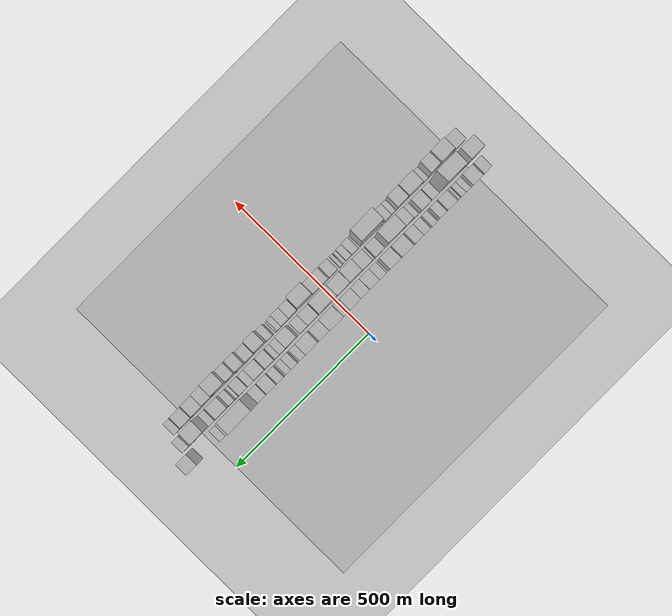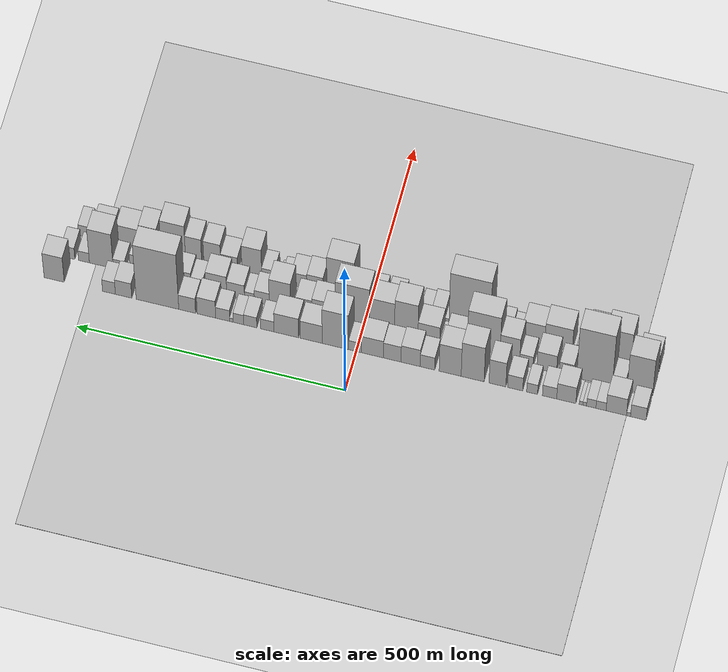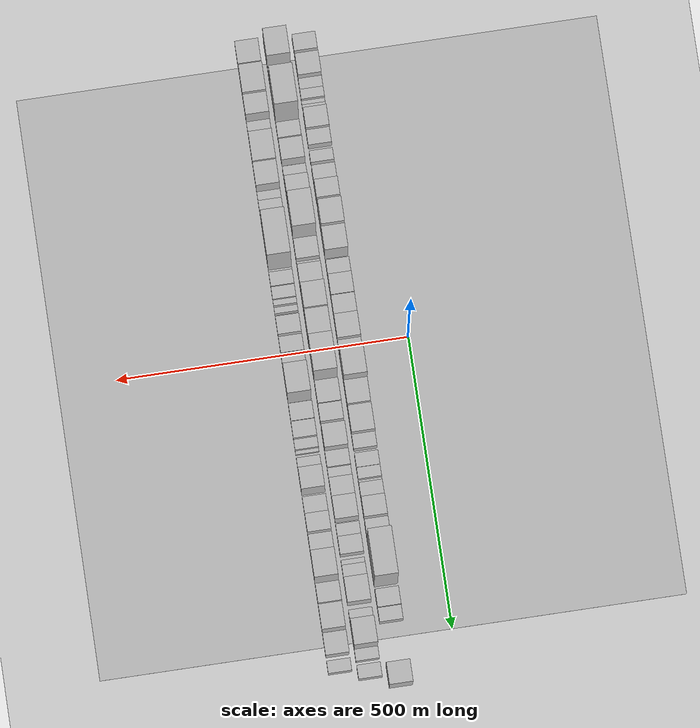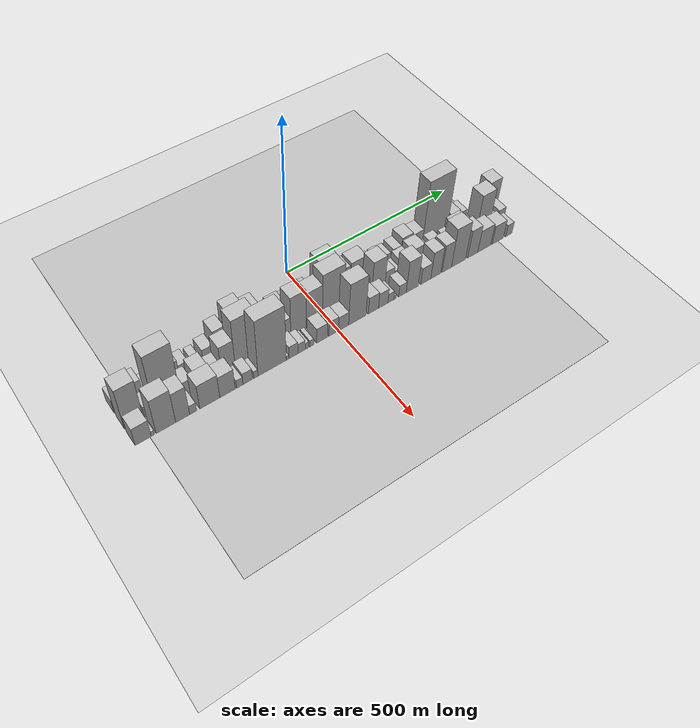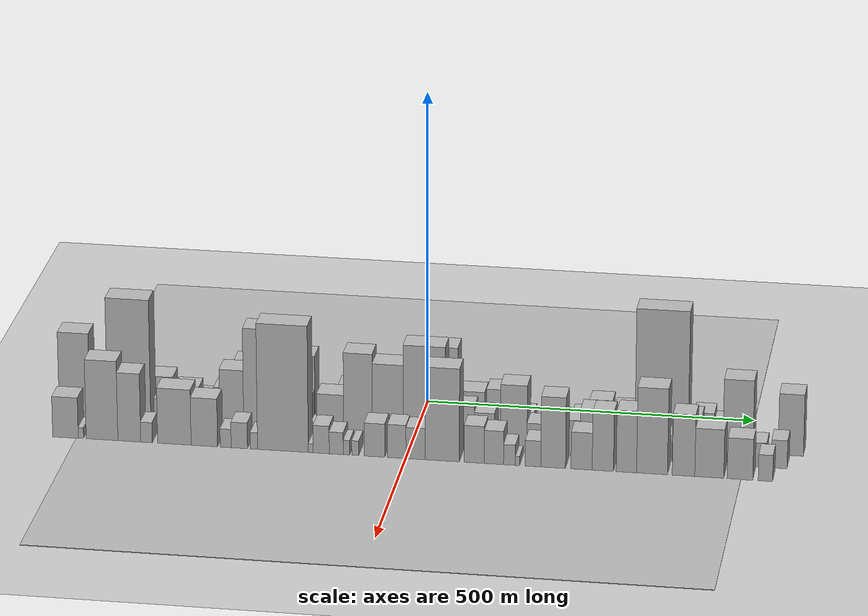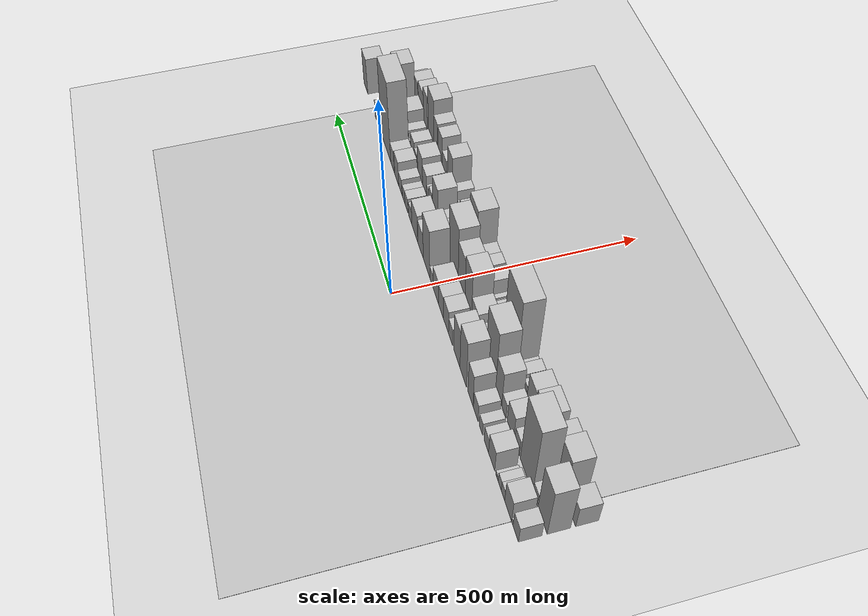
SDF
<?xml version="1.0" encoding="utf-8"?>

<sdf version="1.6">

   <world name="default">

      <gui fullscreen="0">

         <camera name="user_camera">

            <pose>-15 0 4.57585 0 0 0</pose>

            <view_controller>orbit</view_controller>

         </camera>

      </gui>

      <scene>

         <sky>

           <clouds>

             <speed>12</speed>

           </clouds>

         </sky>

         <ambient>0.4 0.4 0.4 1</ambient>

         <background>0.7 0.7 0.7 1</background>

         <shadows>1</shadows>

      </scene>

      <gravity>0 0 -9.8066</gravity>

      <magnetic_field>6e-06 2.3e-05 -4.2e-05</magnetic_field>

      <physics default="0" name="default_physics" type="ode">

         <ode>

            <solver>

               <type>quick</type>

               <iters>10</iters>

               <sor>1.0</sor>

               <use_dynamic_moi_rescaling>0</use_dynamic_moi_rescaling>

            </solver>

            <constraints>

               <cfm>0</cfm>

               <erp>0.2</erp>

               <contact_max_correcting_vel>100</contact_max_correcting_vel>

               <contact_surface_layer>0.001</contact_surface_layer>

            </constraints>

         </ode>

         <max_step_size>0.004</max_step_size>

         <real_time_factor>1</real_time_factor>

         <real_time_update_rate>250</real_time_update_rate>

      </physics>

      <light name="sun" type="directional">

         <cast_shadows>1</cast_shadows>

         <pose>0 0 10 0 0 0</pose>

         <diffuse>0.8 0.8 0.8 1</diffuse>

         <specular>0.2 0.2 0.2 1</specular>

         <attenuation>

            <range>1000</range>

            <constant>0.9</constant>

            <linear>0.01</linear>

            <quadratic>0.001</quadratic>

         </attenuation>

         <direction>-0.5 0.1 -0.9</direction>

      </light>

      <include>

         <name>ground_plane_1</name>

         <uri>model://HANNAS_ground_plane</uri>

         <pose>0 0 0  0 0 0</pose>

      </include>

      <include>

         <name>ground_plane_2</name>

         <uri>model://HANNAS_ground_plane</uri>

         <pose>100 0 0  0 0 0</pose>

      </include>

      <model name="building_1">

         <static>1</static>

         <pose frame="">100.0000 -521.6150 0 0.000000 0.000000 0.000000</pose>

         <link name="link">

            <pose frame="">0 0 25.50 0 0 0</pose>

            <collision name="collision">

               <geometry>

                  <box>

                     <size>40.0000 28.7700 51.0000</size>

                  </box>

               </geometry>

               <max_contacts>10</max_contacts>

               <surface>

                  <contact>

                     <ode/>

                  </contact>

                  <bounce/>

                  <friction>

                     <torsional>

                        <ode/>

                     </torsional>

                     <ode/>

                  </friction>

               </surface>

            </collision>

            <visual name="visual">

               <cast_shadows>0</cast_shadows>

               <geometry>

                  <box>

                     <size>40.0000 28.7700 51.0000</size>

                  </box>

               </geometry>

               <material>

                  <script>

                     <uri>model://HANNAS_wall/materials/scripts</uri>

                     <uri>model://HANNAS_wall/materials/textures</uri>

                     <name>vrc/HANNAS_wall</name>

                  </script>

               </material>

            </visual>

            <self_collide>0</self_collide>

            <enable_wind>0</enable_wind>

            <kinematic>0</kinematic>

         </link>

      </model>

      <model name="building_2">

         <static>1</static>

         <pose frame="">100.0000 -503.5471 0 0.000000 0.000000 0.000000</pose>

         <link name="link">

            <pose frame="">0 0 7.50 0 0 0</pose>

            <collision name="collision">

               <geometry>

                  <box>

                     <size>40.0000 7.3658 15.0000</size>

                  </box>

               </geometry>

               <max_contacts>10</max_contacts>

               <surface>

                  <contact>

                     <ode/>

                  </contact>

                  <bounce/>

                  <friction>

                     <torsional>

                        <ode/>

                     </torsional>

                     <ode/>

                  </friction>

               </surface>

            </collision>

            <visual name="visual">

               <cast_shadows>0</cast_shadows>

               <geometry>

                  <box>

                     <size>40.0000 7.3658 15.0000</size>

                  </box>

               </geometry>

               <material>

                  <script>

                     <uri>model://HANNAS_wall/materials/scripts</uri>

                     <uri>model://HANNAS_wall/materials/textures</uri>

                     <name>vrc/HANNAS_wall</name>

                  </script>

               </material>

            </visual>

            <self_collide>0</self_collide>

            <enable_wind>0</enable_wind>

            <kinematic>0</kinematic>

         </link>

      </model>

      <model name="building_3">

         <static>1</static>

         <pose frame="">100.0000 -481.0259 0 0.000000 0.000000 0.000000</pose>

         <link name="link">

            <pose frame="">0 0 34.50 0 0 0</pose>

            <collision name="collision">

               <geometry>

                  <box>

                     <size>40.0000 37.6766 69.0000</size>

                  </box>

               </geometry>

               <max_contacts>10</max_contacts>

               <surface>

                  <contact>

                     <ode/>

                  </contact>

                  <bounce/>

                  <friction>

                     <torsional>

                        <ode/>

                     </torsional>

                     <ode/>

                  </friction>

               </surface>

            </collision>

            <visual name="visual">

               <cast_shadows>0</cast_shadows>

               <geometry>

                  <box>

                     <size>40.0000 37.6766 69.0000</size>

                  </box>

               </geometry>

               <material>

                  <script>

                     <uri>model://HANNAS_wall/materials/scripts</uri>

                     <uri>model://HANNAS_wall/materials/textures</uri>

                     <name>vrc/HANNAS_wall</name>

                  </script>

               </material>

            </visual>

            <self_collide>0</self_collide>

            <enable_wind>0</enable_wind>

            <kinematic>0</kinematic>

         </link>

      </model>

      <model name="building_4">

         <static>1</static>

         <pose frame="">100.0000 -452.8292 0 0.000000 0.000000 0.000000</pose>

         <link name="link">

            <pose frame="">0 0 16.50 0 0 0</pose>

            <collision name="collision">

               <geometry>

                  <box>

                     <size>40.0000 18.7168 33.0000</size>

                  </box>

               </geometry>

               <max_contacts>10</max_contacts>

               <surface>

                  <contact>

                     <ode/>

                  </contact>

                  <bounce/>

                  <friction>

                     <torsional>

                        <ode/>

                     </torsional>

                     <ode/>

                  </friction>

               </surface>

            </collision>

            <visual name="visual">

               <cast_shadows>0</cast_shadows>

               <geometry>

                  <box>

                     <size>40.0000 18.7168 33.0000</size>

                  </box>

               </geometry>

               <material>

                  <script>

                     <uri>model://HANNAS_wall/materials/scripts</uri>

                     <uri>model://HANNAS_wall/materials/textures</uri>

                     <name>vrc/HANNAS_wall</name>

                  </script>

               </material>

            </visual>

            <self_collide>0</self_collide>

            <enable_wind>0</enable_wind>

            <kinematic>0</kinematic>

         </link>

      </model>

      <model name="building_5">

         <static>1</static>

         <pose frame="">100.0000 -434.8815 0 0.000000 0.000000 0.000000</pose>

         <link name="link">

            <pose frame="">0 0 16.50 0 0 0</pose>

            <collision name="collision">

               <geometry>

                  <box>

                     <size>40.0000 17.1787 33.0000</size>

                  </box>

               </geometry>

               <max_contacts>10</max_contacts>

               <surface>

                  <contact>

                     <ode/>

                  </contact>

                  <bounce/>

                  <friction>

                     <torsional>

                        <ode/>

                     </torsional>

                     <ode/>

                  </friction>

               </surface>

            </collision>

            <visual name="visual">

               <cast_shadows>0</cast_shadows>

               <geometry>

                  <box>

                     <size>40.0000 17.1787 33.0000</size>

                  </box>

               </geometry>

               <material>

                  <script>

                     <uri>model://HANNAS_wall/materials/scripts</uri>

                     <uri>model://HANNAS_wall/materials/textures</uri>

                     <name>vrc/HANNAS_wall</name>

                  </script>

               </material>

            </visual>

            <self_collide>0</self_collide>

            <enable_wind>0</enable_wind>

            <kinematic>0</kinematic>

         </link>

      </model>

      <model name="building_6">

         <static>1</static>

         <pose frame="">100.0000 -422.8432 0 0.000000 0.000000 0.000000</pose>

         <link name="link">

            <pose frame="">0 0 7.50 0 0 0</pose>

            <collision name="collision">

               <geometry>

                  <box>

                     <size>40.0000 6.8978 15.0000</size>

                  </box>

               </geometry>

               <max_contacts>10</max_contacts>

               <surface>

                  <contact>

                     <ode/>

                  </contact>

                  <bounce/>

                  <friction>

                     <torsional>

                        <ode/>

                     </torsional>

                     <ode/>

                  </friction>

               </surface>

            </collision>

            <visual name="visual">

               <cast_shadows>0</cast_shadows>

               <geometry>

                  <box>

                     <size>40.0000 6.8978 15.0000</size>

                  </box>

               </geometry>

               <material>

                  <script>

                     <uri>model://HANNAS_wall/materials/scripts</uri>

                     <uri>model://HANNAS_wall/materials/textures</uri>

                     <name>vrc/HANNAS_wall</name>

                  </script>

               </material>

            </visual>

            <self_collide>0</self_collide>

            <enable_wind>0</enable_wind>

            <kinematic>0</kinematic>

         </link>

      </model>

      <model name="building_7">

         <static>1</static>

         <pose frame="">100.0000 -415.9472 0 0.000000 0.000000 0.000000</pose>

         <link name="link">

            <pose frame="">0 0 7.50 0 0 0</pose>

            <collision name="collision">

               <geometry>

                  <box>

                     <size>40.0000 6.8943 15.0000</size>

                  </box>

               </geometry>

               <max_contacts>10</max_contacts>

               <surface>

                  <contact>

                     <ode/>

                  </contact>

                  <bounce/>

                  <friction>

                     <torsional>

                        <ode/>

                     </torsional>

                     <ode/>

                  </friction>

               </surface>

            </collision>

            <visual name="visual">

               <cast_shadows>0</cast_shadows>

               <geometry>

                  <box>

                     <size>40.0000 6.8943 15.0000</size>

                  </box>

               </geometry>

               <material>

                  <script>

                     <uri>model://HANNAS_wall/materials/scripts</uri>

                     <uri>model://HANNAS_wall/materials/textures</uri>

                     <name>vrc/HANNAS_wall</name>

                  </script>

               </material>

            </visual>

            <self_collide>0</self_collide>

            <enable_wind>0</enable_wind>

            <kinematic>0</kinematic>

         </link>

      </model>

      <model name="building_8">

         <static>1</static>

         <pose frame="">100.0000 -388.7740 0 0.000000 0.000000 0.000000</pose>

         <link name="link">

            <pose frame="">0 0 33.00 0 0 0</pose>

            <collision name="collision">

               <geometry>

                  <box>

                     <size>40.0000 35.4521 66.0000</size>

                  </box>

               </geometry>

               <max_contacts>10</max_contacts>

               <surface>

                  <contact>

                     <ode/>

                  </contact>

                  <bounce/>

                  <friction>

                     <torsional>

                        <ode/>

                     </torsional>

                     <ode/>

                  </friction>

               </surface>

            </collision>

            <visual name="visual">

               <cast_shadows>0</cast_shadows>

               <geometry>

                  <box>

                     <size>40.0000 35.4521 66.0000</size>

                  </box>

               </geometry>

               <material>

                  <script>

                     <uri>model://HANNAS_wall/materials/scripts</uri>

                     <uri>model://HANNAS_wall/materials/textures</uri>

                     <name>vrc/HANNAS_wall</name>

                  </script>

               </material>

            </visual>

            <self_collide>0</self_collide>

            <enable_wind>0</enable_wind>

            <kinematic>0</kinematic>

         </link>

      </model>

      <model name="building_9">

         <static>1</static>

         <pose frame="">100.0000 -357.8860 0 0.000000 0.000000 0.000000</pose>

         <link name="link">

            <pose frame="">0 0 22.50 0 0 0</pose>

            <collision name="collision">

               <geometry>

                  <box>

                     <size>40.0000 26.3239 45.0000</size>

                  </box>

               </geometry>

               <max_contacts>10</max_contacts>

               <surface>

                  <contact>

                     <ode/>

                  </contact>

                  <bounce/>

                  <friction>

                     <torsional>

                        <ode/>

                     </torsional>

                     <ode/>

                  </friction>

               </surface>

            </collision>

            <visual name="visual">

               <cast_shadows>0</cast_shadows>

               <geometry>

                  <box>

                     <size>40.0000 26.3239 45.0000</size>

                  </box>

               </geometry>

               <material>

                  <script>

                     <uri>model://HANNAS_wall/materials/scripts</uri>

                     <uri>model://HANNAS_wall/materials/textures</uri>

                     <name>vrc/HANNAS_wall</name>

                  </script>

               </material>

            </visual>

            <self_collide>0</self_collide>

            <enable_wind>0</enable_wind>

            <kinematic>0</kinematic>

         </link>

      </model>

      <model name="building_10">

         <static>1</static>

         <pose frame="">100.0000 -325.5887 0 0.000000 0.000000 0.000000</pose>

         <link name="link">

            <pose frame="">0 0 19.50 0 0 0</pose>

            <collision name="collision">

               <geometry>

                  <box>

                     <size>40.0000 20.2706 39.0000</size>

                  </box>

               </geometry>

               <max_contacts>10</max_contacts>

               <surface>

                  <contact>

                     <ode/>

                  </contact>

                  <bounce/>

                  <friction>

                     <torsional>

                        <ode/>

                     </torsional>

                     <ode/>

                  </friction>

               </surface>

            </collision>

            <visual name="visual">

               <cast_shadows>0</cast_shadows>

               <geometry>

                  <box>

                     <size>40.0000 20.2706 39.0000</size>

                  </box>

               </geometry>

               <material>

                  <script>

                     <uri>model://HANNAS_wall/materials/scripts</uri>

                     <uri>model://HANNAS_wall/materials/textures</uri>

                     <name>vrc/HANNAS_wall</name>

                  </script>

               </material>

            </visual>

            <self_collide>0</self_collide>

            <enable_wind>0</enable_wind>

            <kinematic>0</kinematic>

         </link>

      </model>

      <model name="building_11">

         <static>1</static>

         <pose frame="">100.0000 -294.3115 0 0.000000 0.000000 0.000000</pose>

         <link name="link">

            <pose frame="">0 0 27.00 0 0 0</pose>

            <collision name="collision">

               <geometry>

                  <box>

                     <size>40.0000 28.2839 54.0000</size>

                  </box>

               </geometry>

               <max_contacts>10</max_contacts>

               <surface>

                  <contact>

                     <ode/>

                  </contact>

                  <bounce/>

                  <friction>

                     <torsional>

                        <ode/>

                     </torsional>

                     <ode/>

                  </friction>

               </surface>

            </collision>

            <visual name="visual">

               <cast_shadows>0</cast_shadows>

               <geometry>

                  <box>

                     <size>40.0000 28.2839 54.0000</size>

                  </box>

               </geometry>

               <material>

                  <script>

                     <uri>model://HANNAS_wall/materials/scripts</uri>

                     <uri>model://HANNAS_wall/materials/textures</uri>

                     <name>vrc/HANNAS_wall</name>

                  </script>

               </material>

            </visual>

            <self_collide>0</self_collide>

            <enable_wind>0</enable_wind>

            <kinematic>0</kinematic>

         </link>

      </model>

      <model name="building_12">

         <static>1</static>

         <pose frame="">100.0000 -261.5331 0 0.000000 0.000000 0.000000</pose>

         <link name="link">

            <pose frame="">0 0 49.50 0 0 0</pose>

            <collision name="collision">

               <geometry>

                  <box>

                     <size>40.0000 31.2730 99.0000</size>

                  </box>

               </geometry>

               <max_contacts>10</max_contacts>

               <surface>

                  <contact>

                     <ode/>

                  </contact>

                  <bounce/>

                  <friction>

                     <torsional>

                        <ode/>

                     </torsional>

                     <ode/>

                  </friction>

               </surface>

            </collision>

            <visual name="visual">

               <cast_shadows>0</cast_shadows>

               <geometry>

                  <box>

                     <size>40.0000 31.2730 99.0000</size>

                  </box>

               </geometry>

               <material>

                  <script>

                     <uri>model://HANNAS_wall/materials/scripts</uri>

                     <uri>model://HANNAS_wall/materials/textures</uri>

                     <name>vrc/HANNAS_wall</name>

                  </script>

               </material>

            </visual>

            <self_collide>0</self_collide>

            <enable_wind>0</enable_wind>

            <kinematic>0</kinematic>

         </link>

      </model>

      <model name="building_13">

         <static>1</static>

         <pose frame="">100.0000 -215.6549 0 0.000000 0.000000 0.000000</pose>

         <link name="link">

            <pose frame="">0 0 70.50 0 0 0</pose>

            <collision name="collision">

               <geometry>

                  <box>

                     <size>40.0000 42.4833 141.0000</size>

                  </box>

               </geometry>

               <max_contacts>10</max_contacts>

               <surface>

                  <contact>

                     <ode/>

                  </contact>

                  <bounce/>

                  <friction>

                     <torsional>

                        <ode/>

                     </torsional>

                     <ode/>

                  </friction>

               </surface>

            </collision>

            <visual name="visual">

               <cast_shadows>0</cast_shadows>

               <geometry>

                  <box>

                     <size>40.0000 42.4833 141.0000</size>

                  </box>

               </geometry>

               <material>

                  <script>

                     <uri>model://HANNAS_wall/materials/scripts</uri>

                     <uri>model://HANNAS_wall/materials/textures</uri>

                     <name>vrc/HANNAS_wall</name>

                  </script>

               </material>

            </visual>

            <self_collide>0</self_collide>

            <enable_wind>0</enable_wind>

            <kinematic>0</kinematic>

         </link>

      </model>

      <model name="building_14">

         <static>1</static>

         <pose frame="">100.0000 -174.0290 0 0.000000 0.000000 0.000000</pose>

         <link name="link">

            <pose frame="">0 0 57.00 0 0 0</pose>

            <collision name="collision">

               <geometry>

                  <box>

                     <size>40.0000 40.7685 114.0000</size>

                  </box>

               </geometry>

               <max_contacts>10</max_contacts>

               <surface>

                  <contact>

                     <ode/>

                  </contact>

                  <bounce/>

                  <friction>

                     <torsional>

                        <ode/>

                     </torsional>

                     <ode/>

                  </friction>

               </surface>

            </collision>

            <visual name="visual">

               <cast_shadows>0</cast_shadows>

               <geometry>

                  <box>

                     <size>40.0000 40.7685 114.0000</size>

                  </box>

               </geometry>

               <material>

                  <script>

                     <uri>model://HANNAS_wall/materials/scripts</uri>

                     <uri>model://HANNAS_wall/materials/textures</uri>

                     <name>vrc/HANNAS_wall</name>

                  </script>

               </material>

            </visual>

            <self_collide>0</self_collide>

            <enable_wind>0</enable_wind>

            <kinematic>0</kinematic>

         </link>

      </model>

      <model name="building_15">

         <static>1</static>

         <pose frame="">100.0000 -132.1360 0 0.000000 0.000000 0.000000</pose>

         <link name="link">

            <pose frame="">0 0 25.50 0 0 0</pose>

            <collision name="collision">

               <geometry>

                  <box>

                     <size>40.0000 27.0176 51.0000</size>

                  </box>

               </geometry>

               <max_contacts>10</max_contacts>

               <surface>

                  <contact>

                     <ode/>

                  </contact>

                  <bounce/>

                  <friction>

                     <torsional>

                        <ode/>

                     </torsional>

                     <ode/>

                  </friction>

               </surface>

            </collision>

            <visual name="visual">

               <cast_shadows>0</cast_shadows>

               <geometry>

                  <box>

                     <size>40.0000 27.0176 51.0000</size>

                  </box>

               </geometry>

               <material>

                  <script>

                     <uri>model://HANNAS_wall/materials/scripts</uri>

                     <uri>model://HANNAS_wall/materials/textures</uri>

                     <name>vrc/HANNAS_wall</name>

                  </script>

               </material>

            </visual>

            <self_collide>0</self_collide>

            <enable_wind>0</enable_wind>

            <kinematic>0</kinematic>

         </link>

      </model>

      <model name="building_16">

         <static>1</static>

         <pose frame="">100.0000 -100.8448 0 0.000000 0.000000 0.000000</pose>

         <link name="link">

            <pose frame="">0 0 34.50 0 0 0</pose>

            <collision name="collision">

               <geometry>

                  <box>

                     <size>40.0000 35.5646 69.0000</size>

                  </box>

               </geometry>

               <max_contacts>10</max_contacts>

               <surface>

                  <contact>

                     <ode/>

                  </contact>

                  <bounce/>

                  <friction>

                     <torsional>

                        <ode/>

                     </torsional>

                     <ode/>

                  </friction>

               </surface>

            </collision>

            <visual name="visual">

               <cast_shadows>0</cast_shadows>

               <geometry>

                  <box>

                     <size>40.0000 35.5646 69.0000</size>

                  </box>

               </geometry>

               <material>

                  <script>

                     <uri>model://HANNAS_wall/materials/scripts</uri>

                     <uri>model://HANNAS_wall/materials/textures</uri>

                     <name>vrc/HANNAS_wall</name>

                  </script>

               </material>

            </visual>

            <self_collide>0</self_collide>

            <enable_wind>0</enable_wind>

            <kinematic>0</kinematic>

         </link>

      </model>

      <model name="building_17">

         <static>1</static>

         <pose frame="">100.0000 -66.6358 0 0.000000 0.000000 0.000000</pose>

         <link name="link">

            <pose frame="">0 0 31.50 0 0 0</pose>

            <collision name="collision">

               <geometry>

                  <box>

                     <size>40.0000 32.8534 63.0000</size>

                  </box>

               </geometry>

               <max_contacts>10</max_contacts>

               <surface>

                  <contact>

                     <ode/>

                  </contact>

                  <bounce/>

                  <friction>

                     <torsional>

                        <ode/>

                     </torsional>

                     <ode/>

                  </friction>

               </surface>

            </collision>

            <visual name="visual">

               <cast_shadows>0</cast_shadows>

               <geometry>

                  <box>

                     <size>40.0000 32.8534 63.0000</size>

                  </box>

               </geometry>

               <material>

                  <script>

                     <uri>model://HANNAS_wall/materials/scripts</uri>

                     <uri>model://HANNAS_wall/materials/textures</uri>

                     <name>vrc/HANNAS_wall</name>

                  </script>

               </material>

            </visual>

            <self_collide>0</self_collide>

            <enable_wind>0</enable_wind>

            <kinematic>0</kinematic>

         </link>

      </model>

      <model name="building_18">

         <static>1</static>

         <pose frame="">100.0000 -29.5664 0 0.000000 0.000000 0.000000</pose>

         <link name="link">

            <pose frame="">0 0 34.50 0 0 0</pose>

            <collision name="collision">

               <geometry>

                  <box>

                     <size>40.0000 41.2854 69.0000</size>

                  </box>

               </geometry>

               <max_contacts>10</max_contacts>

               <surface>

                  <contact>

                     <ode/>

                  </contact>

                  <bounce/>

                  <friction>

                     <torsional>

                        <ode/>

                     </torsional>

                     <ode/>

                  </friction>

               </surface>

            </collision>

            <visual name="visual">

               <cast_shadows>0</cast_shadows>

               <geometry>

                  <box>

                     <size>40.0000 41.2854 69.0000</size>

                  </box>

               </geometry>

               <material>

                  <script>

                     <uri>model://HANNAS_wall/materials/scripts</uri>

                     <uri>model://HANNAS_wall/materials/textures</uri>

                     <name>vrc/HANNAS_wall</name>

                  </script>

               </material>

            </visual>

            <self_collide>0</self_collide>

            <enable_wind>0</enable_wind>

            <kinematic>0</kinematic>

         </link>

      </model>

      <model name="building_19">

         <static>1</static>

         <pose frame="">100.0000 2.6886 0 0.000000 0.000000 0.000000</pose>

         <link name="link">

            <pose frame="">0 0 19.50 0 0 0</pose>

            <collision name="collision">

               <geometry>

                  <box>

                     <size>40.0000 23.2246 39.0000</size>

                  </box>

               </geometry>

               <max_contacts>10</max_contacts>

               <surface>

                  <contact>

                     <ode/>

                  </contact>

                  <bounce/>

                  <friction>

                     <torsional>

                        <ode/>

                     </torsional>

                     <ode/>

                  </friction>

               </surface>

            </collision>

            <visual name="visual">

               <cast_shadows>0</cast_shadows>

               <geometry>

                  <box>

                     <size>40.0000 23.2246 39.0000</size>

                  </box>

               </geometry>

               <material>

                  <script>

                     <uri>model://HANNAS_wall/materials/scripts</uri>

                     <uri>model://HANNAS_wall/materials/textures</uri>

                     <name>vrc/HANNAS_wall</name>

                  </script>

               </material>

            </visual>

            <self_collide>0</self_collide>

            <enable_wind>0</enable_wind>

            <kinematic>0</kinematic>

         </link>

      </model>

      <model name="building_20">

         <static>1</static>

         <pose frame="">100.0000 38.9551 0 0.000000 0.000000 0.000000</pose>

         <link name="link">

            <pose frame="">0 0 70.50 0 0 0</pose>

            <collision name="collision">

               <geometry>

                  <box>

                     <size>40.0000 49.3084 141.0000</size>

                  </box>

               </geometry>

               <max_contacts>10</max_contacts>

               <surface>

                  <contact>

                     <ode/>

                  </contact>

                  <bounce/>

                  <friction>

                     <torsional>

                        <ode/>

                     </torsional>

                     <ode/>

                  </friction>

               </surface>

            </collision>

            <visual name="visual">

               <cast_shadows>0</cast_shadows>

               <geometry>

                  <box>

                     <size>40.0000 49.3084 141.0000</size>

                  </box>

               </geometry>

               <material>

                  <script>

                     <uri>model://HANNAS_wall/materials/scripts</uri>

                     <uri>model://HANNAS_wall/materials/textures</uri>

                     <name>vrc/HANNAS_wall</name>

                  </script>

               </material>

            </visual>

            <self_collide>0</self_collide>

            <enable_wind>0</enable_wind>

            <kinematic>0</kinematic>

         </link>

      </model>

      <model name="building_21">

         <static>1</static>

         <pose frame="">100.0000 84.0371 0 0.000000 0.000000 0.000000</pose>

         <link name="link">

            <pose frame="">0 0 36.00 0 0 0</pose>

            <collision name="collision">

               <geometry>

                  <box>

                     <size>40.0000 40.8557 72.0000</size>

                  </box>

               </geometry>

               <max_contacts>10</max_contacts>

               <surface>

                  <contact>

                     <ode/>

                  </contact>

                  <bounce/>

                  <friction>

                     <torsional>

                        <ode/>

                     </torsional>

                     <ode/>

                  </friction>

               </surface>

            </collision>

            <visual name="visual">

               <cast_shadows>0</cast_shadows>

               <geometry>

                  <box>

                     <size>40.0000 40.8557 72.0000</size>

                  </box>

               </geometry>

               <material>

                  <script>

                     <uri>model://HANNAS_wall/materials/scripts</uri>

                     <uri>model://HANNAS_wall/materials/textures</uri>

                     <name>vrc/HANNAS_wall</name>

                  </script>

               </material>

            </visual>

            <self_collide>0</self_collide>

            <enable_wind>0</enable_wind>

            <kinematic>0</kinematic>

         </link>

      </model>

      <model name="building_22">

         <static>1</static>

         <pose frame="">100.0000 130.4165 0 0.000000 0.000000 0.000000</pose>

         <link name="link">

            <pose frame="">0 0 39.00 0 0 0</pose>

            <collision name="collision">

               <geometry>

                  <box>

                     <size>40.0000 45.9031 78.0000</size>

                  </box>

               </geometry>

               <max_contacts>10</max_contacts>

               <surface>

                  <contact>

                     <ode/>

                  </contact>

                  <bounce/>

                  <friction>

                     <torsional>

                        <ode/>

                     </torsional>

                     <ode/>

                  </friction>

               </surface>

            </collision>

            <visual name="visual">

               <cast_shadows>0</cast_shadows>

               <geometry>

                  <box>

                     <size>40.0000 45.9031 78.0000</size>

                  </box>

               </geometry>

               <material>

                  <script>

                     <uri>model://HANNAS_wall/materials/scripts</uri>

                     <uri>model://HANNAS_wall/materials/textures</uri>

                     <name>vrc/HANNAS_wall</name>

                  </script>

               </material>

            </visual>

            <self_collide>0</self_collide>

            <enable_wind>0</enable_wind>

            <kinematic>0</kinematic>

         </link>

      </model>

      <model name="building_23">

         <static>1</static>

         <pose frame="">100.0000 165.8833 0 0.000000 0.000000 0.000000</pose>

         <link name="link">

            <pose frame="">0 0 21.00 0 0 0</pose>

            <collision name="collision">

               <geometry>

                  <box>

                     <size>40.0000 25.0304 42.0000</size>

                  </box>

               </geometry>

               <max_contacts>10</max_contacts>

               <surface>

                  <contact>

                     <ode/>

                  </contact>

                  <bounce/>

                  <friction>

                     <torsional>

                        <ode/>

                     </torsional>

                     <ode/>

                  </friction>

               </surface>

            </collision>

            <visual name="visual">

               <cast_shadows>0</cast_shadows>

               <geometry>

                  <box>

                     <size>40.0000 25.0304 42.0000</size>

                  </box>

               </geometry>

               <material>

                  <script>

                     <uri>model://HANNAS_wall/materials/scripts</uri>

                     <uri>model://HANNAS_wall/materials/textures</uri>

                     <name>vrc/HANNAS_wall</name>

                  </script>

               </material>

            </visual>

            <self_collide>0</self_collide>

            <enable_wind>0</enable_wind>

            <kinematic>0</kinematic>

         </link>

      </model>

      <model name="building_24">

         <static>1</static>

         <pose frame="">100.0000 197.6882 0 0.000000 0.000000 0.000000</pose>

         <link name="link">

            <pose frame="">0 0 21.00 0 0 0</pose>

            <collision name="collision">

               <geometry>

                  <box>

                     <size>40.0000 24.5794 42.0000</size>

                  </box>

               </geometry>

               <max_contacts>10</max_contacts>

               <surface>

                  <contact>

                     <ode/>

                  </contact>

                  <bounce/>

                  <friction>

                     <torsional>

                        <ode/>

                     </torsional>

                     <ode/>

                  </friction>

               </surface>

            </collision>

            <visual name="visual">

               <cast_shadows>0</cast_shadows>

               <geometry>

                  <box>

                     <size>40.0000 24.5794 42.0000</size>

                  </box>

               </geometry>

               <material>

                  <script>

                     <uri>model://HANNAS_wall/materials/scripts</uri>

                     <uri>model://HANNAS_wall/materials/textures</uri>

                     <name>vrc/HANNAS_wall</name>

                  </script>

               </material>

            </visual>

            <self_collide>0</self_collide>

            <enable_wind>0</enable_wind>

            <kinematic>0</kinematic>

         </link>

      </model>

      <model name="building_25">

         <static>1</static>

         <pose frame="">100.0000 219.7532 0 0.000000 0.000000 0.000000</pose>

         <link name="link">

            <pose frame="">0 0 19.50 0 0 0</pose>

            <collision name="collision">

               <geometry>

                  <box>

                     <size>40.0000 19.5507 39.0000</size>

                  </box>

               </geometry>

               <max_contacts>10</max_contacts>

               <surface>

                  <contact>

                     <ode/>

                  </contact>

                  <bounce/>

                  <friction>

                     <torsional>

                        <ode/>

                     </torsional>

                     <ode/>

                  </friction>

               </surface>

            </collision>

            <visual name="visual">

               <cast_shadows>0</cast_shadows>

               <geometry>

                  <box>

                     <size>40.0000 19.5507 39.0000</size>

                  </box>

               </geometry>

               <material>

                  <script>

                     <uri>model://HANNAS_wall/materials/scripts</uri>

                     <uri>model://HANNAS_wall/materials/textures</uri>

                     <name>vrc/HANNAS_wall</name>

                  </script>

               </material>

            </visual>

            <self_collide>0</self_collide>

            <enable_wind>0</enable_wind>

            <kinematic>0</kinematic>

         </link>

      </model>

      <model name="building_26">

         <static>1</static>

         <pose frame="">100.0000 232.7908 0 0.000000 0.000000 0.000000</pose>

         <link name="link">

            <pose frame="">0 0 7.50 0 0 0</pose>

            <collision name="collision">

               <geometry>

                  <box>

                     <size>40.0000 6.5244 15.0000</size>

                  </box>

               </geometry>

               <max_contacts>10</max_contacts>

               <surface>

                  <contact>

                     <ode/>

                  </contact>

                  <bounce/>

                  <friction>

                     <torsional>

                        <ode/>

                     </torsional>

                     <ode/>

                  </friction>

               </surface>

            </collision>

            <visual name="visual">

               <cast_shadows>0</cast_shadows>

               <geometry>

                  <box>

                     <size>40.0000 6.5244 15.0000</size>

                  </box>

               </geometry>

               <material>

                  <script>

                     <uri>model://HANNAS_wall/materials/scripts</uri>

                     <uri>model://HANNAS_wall/materials/textures</uri>

                     <name>vrc/HANNAS_wall</name>

                  </script>

               </material>

            </visual>

            <self_collide>0</self_collide>

            <enable_wind>0</enable_wind>

            <kinematic>0</kinematic>

         </link>

      </model>

      <model name="building_27">

         <static>1</static>

         <pose frame="">100.0000 249.0915 0 0.000000 0.000000 0.000000</pose>

         <link name="link">

            <pose frame="">0 0 22.50 0 0 0</pose>

            <collision name="collision">

               <geometry>

                  <box>

                     <size>40.0000 26.0770 45.0000</size>

                  </box>

               </geometry>

               <max_contacts>10</max_contacts>

               <surface>

                  <contact>

                     <ode/>

                  </contact>

                  <bounce/>

                  <friction>

                     <torsional>

                        <ode/>

                     </torsional>

                     <ode/>

                  </friction>

               </surface>

            </collision>

            <visual name="visual">

               <cast_shadows>0</cast_shadows>

               <geometry>

                  <box>

                     <size>40.0000 26.0770 45.0000</size>

                  </box>

               </geometry>

               <material>

                  <script>

                     <uri>model://HANNAS_wall/materials/scripts</uri>

                     <uri>model://HANNAS_wall/materials/textures</uri>

                     <name>vrc/HANNAS_wall</name>

                  </script>

               </material>

            </visual>

            <self_collide>0</self_collide>

            <enable_wind>0</enable_wind>

            <kinematic>0</kinematic>

         </link>

      </model>

      <model name="building_28">

         <static>1</static>

         <pose frame="">100.0000 279.5010 0 0.000000 0.000000 0.000000</pose>

         <link name="link">

            <pose frame="">0 0 34.50 0 0 0</pose>

            <collision name="collision">

               <geometry>

                  <box>

                     <size>40.0000 34.7419 69.0000</size>

                  </box>

               </geometry>

               <max_contacts>10</max_contacts>

               <surface>

                  <contact>

                     <ode/>

                  </contact>

                  <bounce/>

                  <friction>

                     <torsional>

                        <ode/>

                     </torsional>

                     <ode/>

                  </friction>

               </surface>

            </collision>

            <visual name="visual">

               <cast_shadows>0</cast_shadows>

               <geometry>

                  <box>

                     <size>40.0000 34.7419 69.0000</size>

                  </box>

               </geometry>

               <material>

                  <script>

                     <uri>model://HANNAS_wall/materials/scripts</uri>

                     <uri>model://HANNAS_wall/materials/textures</uri>

                     <name>vrc/HANNAS_wall</name>

                  </script>

               </material>

            </visual>

            <self_collide>0</self_collide>

            <enable_wind>0</enable_wind>

            <kinematic>0</kinematic>

         </link>

      </model>

      <model name="building_29">

         <static>1</static>

         <pose frame="">100.0000 315.5436 0 0.000000 0.000000 0.000000</pose>

         <link name="link">

            <pose frame="">0 0 30.00 0 0 0</pose>

            <collision name="collision">

               <geometry>

                  <box>

                     <size>40.0000 31.3432 60.0000</size>

                  </box>

               </geometry>

               <max_contacts>10</max_contacts>

               <surface>

                  <contact>

                     <ode/>

                  </contact>

                  <bounce/>

                  <friction>

                     <torsional>

                        <ode/>

                     </torsional>

                     <ode/>

                  </friction>

               </surface>

            </collision>

            <visual name="visual">

               <cast_shadows>0</cast_shadows>

               <geometry>

                  <box>

                     <size>40.0000 31.3432 60.0000</size>

                  </box>

               </geometry>

               <material>

                  <script>

                     <uri>model://HANNAS_wall/materials/scripts</uri>

                     <uri>model://HANNAS_wall/materials/textures</uri>

                     <name>vrc/HANNAS_wall</name>

                  </script>

               </material>

            </visual>

            <self_collide>0</self_collide>

            <enable_wind>0</enable_wind>

            <kinematic>0</kinematic>

         </link>

      </model>

      <model name="building_30">

         <static>1</static>

         <pose frame="">100.0000 371.1281 0 0.000000 0.000000 0.000000</pose>

         <link name="link">

            <pose frame="">0 0 111.00 0 0 0</pose>

            <collision name="collision">

               <geometry>

                  <box>

                     <size>40.0000 79.8259 222.0000</size>

                  </box>

               </geometry>

               <max_contacts>10</max_contacts>

               <surface>

                  <contact>

                     <ode/>

                  </contact>

                  <bounce/>

                  <friction>

                     <torsional>

                        <ode/>

                     </torsional>

                     <ode/>

                  </friction>

               </surface>

            </collision>

            <visual name="visual">

               <cast_shadows>0</cast_shadows>

               <geometry>

                  <box>

                     <size>40.0000 79.8259 222.0000</size>

                  </box>

               </geometry>

               <material>

                  <script>

                     <uri>model://HANNAS_wall/materials/scripts</uri>

                     <uri>model://HANNAS_wall/materials/textures</uri>

                     <name>vrc/HANNAS_wall</name>

                  </script>

               </material>

            </visual>

            <self_collide>0</self_collide>

            <enable_wind>0</enable_wind>

            <kinematic>0</kinematic>

         </link>

      </model>

      <model name="building_31">

         <static>1</static>

         <pose frame="">100.0000 434.5013 0 0.000000 0.000000 0.000000</pose>

         <link name="link">

            <pose frame="">0 0 30.00 0 0 0</pose>

            <collision name="collision">

               <geometry>

                  <box>

                     <size>40.0000 30.9204 60.0000</size>

                  </box>

               </geometry>

               <max_contacts>10</max_contacts>

               <surface>

                  <contact>

                     <ode/>

                  </contact>

                  <bounce/>

                  <friction>

                     <torsional>

                        <ode/>

                     </torsional>

                     <ode/>

                  </friction>

               </surface>

            </collision>

            <visual name="visual">

               <cast_shadows>0</cast_shadows>

               <geometry>

                  <box>

                     <size>40.0000 30.9204 60.0000</size>

                  </box>

               </geometry>

               <material>

                  <script>

                     <uri>model://HANNAS_wall/materials/scripts</uri>

                     <uri>model://HANNAS_wall/materials/textures</uri>

                     <name>vrc/HANNAS_wall</name>

                  </script>

               </material>

            </visual>

            <self_collide>0</self_collide>

            <enable_wind>0</enable_wind>

            <kinematic>0</kinematic>

         </link>

      </model>

      <model name="building_32">

         <static>1</static>

         <pose frame="">100.0000 462.0291 0 0.000000 0.000000 0.000000</pose>

         <link name="link">

            <pose frame="">0 0 24.00 0 0 0</pose>

            <collision name="collision">

               <geometry>

                  <box>

                     <size>40.0000 24.1351 48.0000</size>

                  </box>

               </geometry>

               <max_contacts>10</max_contacts>

               <surface>

                  <contact>

                     <ode/>

                  </contact>

                  <bounce/>

                  <friction>

                     <torsional>

                        <ode/>

                     </torsional>

                     <ode/>

                  </friction>

               </surface>

            </collision>

            <visual name="visual">

               <cast_shadows>0</cast_shadows>

               <geometry>

                  <box>

                     <size>40.0000 24.1351 48.0000</size>

                  </box>

               </geometry>

               <material>

                  <script>

                     <uri>model://HANNAS_wall/materials/scripts</uri>

                     <uri>model://HANNAS_wall/materials/textures</uri>

                     <name>vrc/HANNAS_wall</name>

                  </script>

               </material>

            </visual>

            <self_collide>0</self_collide>

            <enable_wind>0</enable_wind>

            <kinematic>0</kinematic>

         </link>

      </model>

      <model name="building_33">

         <static>1</static>

         <pose frame="">100.0000 564.8013 0 0.000000 0.000000 0.000000</pose>

         <link name="link">

            <pose frame="">0 0 49.50 0 0 0</pose>

            <collision name="collision">

               <geometry>

                  <box>

                     <size>40.0000 37.8031 99.0000</size>

                  </box>

               </geometry>

               <max_contacts>10</max_contacts>

               <surface>

                  <contact>

                     <ode/>

                  </contact>

                  <bounce/>

                  <friction>

                     <torsional>

                        <ode/>

                     </torsional>

                     <ode/>

                  </friction>

               </surface>

            </collision>

            <visual name="visual">

               <cast_shadows>0</cast_shadows>

               <geometry>

                  <box>

                     <size>40.0000 37.8031 99.0000</size>

                  </box>

               </geometry>

               <material>

                  <script>

                     <uri>model://HANNAS_wall/materials/scripts</uri>

                     <uri>model://HANNAS_wall/materials/textures</uri>

                     <name>vrc/HANNAS_wall</name>

                  </script>

               </material>

            </visual>

            <self_collide>0</self_collide>

            <enable_wind>0</enable_wind>

            <kinematic>0</kinematic>

         </link>

      </model>

      <model name="building_34">

         <static>1</static>

         <pose frame="">149.0000 -512.4426 0 0.000000 0.000000 0.000000</pose>

         <link name="link">

            <pose frame="">0 0 75.00 0 0 0</pose>

            <collision name="collision">

               <geometry>

                  <box>

                     <size>40.0000 47.1148 150.0000</size>

                  </box>

               </geometry>

               <max_contacts>10</max_contacts>

               <surface>

                  <contact>

                     <ode/>

                  </contact>

                  <bounce/>

                  <friction>

                     <torsional>

                        <ode/>

                     </torsional>

                     <ode/>

                  </friction>

               </surface>

            </collision>

            <visual name="visual">

               <cast_shadows>0</cast_shadows>

               <geometry>

                  <box>

                     <size>40.0000 47.1148 150.0000</size>

                  </box>

               </geometry>

               <material>

                  <script>

                     <uri>model://HANNAS_wall/materials/scripts</uri>

                     <uri>model://HANNAS_wall/materials/textures</uri>

                     <name>vrc/HANNAS_wall</name>

                  </script>

               </material>

            </visual>

            <self_collide>0</self_collide>

            <enable_wind>0</enable_wind>

            <kinematic>0</kinematic>

         </link>

      </model>

      <model name="building_35">

         <static>1</static>

         <pose frame="">149.0000 -473.7912 0 0.000000 0.000000 0.000000</pose>

         <link name="link">

            <pose frame="">0 0 21.00 0 0 0</pose>

            <collision name="collision">

               <geometry>

                  <box>

                     <size>40.0000 24.1881 42.0000</size>

                  </box>

               </geometry>

               <max_contacts>10</max_contacts>

               <surface>

                  <contact>

                     <ode/>

                  </contact>

                  <bounce/>

                  <friction>

                     <torsional>

                        <ode/>

                     </torsional>

                     <ode/>

                  </friction>

               </surface>

            </collision>

            <visual name="visual">

               <cast_shadows>0</cast_shadows>

               <geometry>

                  <box>

                     <size>40.0000 24.1881 42.0000</size>

                  </box>

               </geometry>

               <material>

                  <script>

                     <uri>model://HANNAS_wall/materials/scripts</uri>

                     <uri>model://HANNAS_wall/materials/textures</uri>

                     <name>vrc/HANNAS_wall</name>

                  </script>

               </material>

            </visual>

            <self_collide>0</self_collide>

            <enable_wind>0</enable_wind>

            <kinematic>0</kinematic>

         </link>

      </model>

      <model name="building_36">

         <static>1</static>

         <pose frame="">149.0000 -428.6505 0 0.000000 0.000000 0.000000</pose>

         <link name="link">

            <pose frame="">0 0 105.00 0 0 0</pose>

            <collision name="collision">

               <geometry>

                  <box>

                     <size>40.0000 66.0934 210.0000</size>

                  </box>

               </geometry>

               <max_contacts>10</max_contacts>

               <surface>

                  <contact>

                     <ode/>

                  </contact>

                  <bounce/>

                  <friction>

                     <torsional>

                        <ode/>

                     </torsional>

                     <ode/>

                  </friction>

               </surface>

            </collision>

            <visual name="visual">

               <cast_shadows>0</cast_shadows>

               <geometry>

                  <box>

                     <size>40.0000 66.0934 210.0000</size>

                  </box>

               </geometry>

               <material>

                  <script>

                     <uri>model://HANNAS_wall/materials/scripts</uri>

                     <uri>model://HANNAS_wall/materials/textures</uri>

                     <name>vrc/HANNAS_wall</name>

                  </script>

               </material>

            </visual>

            <self_collide>0</self_collide>

            <enable_wind>0</enable_wind>

            <kinematic>0</kinematic>

         </link>

      </model>

      <model name="building_37">

         <static>1</static>

         <pose frame="">149.0000 -377.1060 0 0.000000 0.000000 0.000000</pose>

         <link name="link">

            <pose frame="">0 0 25.50 0 0 0</pose>

            <collision name="collision">

               <geometry>

                  <box>

                     <size>40.0000 26.9956 51.0000</size>

                  </box>

               </geometry>

               <max_contacts>10</max_contacts>

               <surface>

                  <contact>

                     <ode/>

                  </contact>

                  <bounce/>

                  <friction>

                     <torsional>

                        <ode/>

                     </torsional>

                     <ode/>

                  </friction>

               </surface>

            </collision>

            <visual name="visual">

               <cast_shadows>0</cast_shadows>

               <geometry>

                  <box>

                     <size>40.0000 26.9956 51.0000</size>

                  </box>

               </geometry>

               <material>

                  <script>

                     <uri>model://HANNAS_wall/materials/scripts</uri>

                     <uri>model://HANNAS_wall/materials/textures</uri>

                     <name>vrc/HANNAS_wall</name>

                  </script>

               </material>

            </visual>

            <self_collide>0</self_collide>

            <enable_wind>0</enable_wind>

            <kinematic>0</kinematic>

         </link>

      </model>

      <model name="building_38">

         <static>1</static>

         <pose frame="">149.0000 -340.4035 0 0.000000 0.000000 0.000000</pose>

         <link name="link">

            <pose frame="">0 0 36.00 0 0 0</pose>

            <collision name="collision">

               <geometry>

                  <box>

                     <size>40.0000 36.4095 72.0000</size>

                  </box>

               </geometry>

               <max_contacts>10</max_contacts>

               <surface>

                  <contact>

                     <ode/>

                  </contact>

                  <bounce/>

                  <friction>

                     <torsional>

                        <ode/>

                     </torsional>

                     <ode/>

                  </friction>

               </surface>

            </collision>

            <visual name="visual">

               <cast_shadows>0</cast_shadows>

               <geometry>

                  <box>

                     <size>40.0000 36.4095 72.0000</size>

                  </box>

               </geometry>

               <material>

                  <script>

                     <uri>model://HANNAS_wall/materials/scripts</uri>

                     <uri>model://HANNAS_wall/materials/textures</uri>

                     <name>vrc/HANNAS_wall</name>

                  </script>

               </material>

            </visual>

            <self_collide>0</self_collide>

            <enable_wind>0</enable_wind>

            <kinematic>0</kinematic>

         </link>

      </model>

      <model name="building_39">

         <static>1</static>

         <pose frame="">149.0000 -302.6995 0 0.000000 0.000000 0.000000</pose>

         <link name="link">

            <pose frame="">0 0 22.50 0 0 0</pose>

            <collision name="collision">

               <geometry>

                  <box>

                     <size>40.0000 24.9985 45.0000</size>

                  </box>

               </geometry>

               <max_contacts>10</max_contacts>

               <surface>

                  <contact>

                     <ode/>

                  </contact>

                  <bounce/>

                  <friction>

                     <torsional>

                        <ode/>

                     </torsional>

                     <ode/>

                  </friction>

               </surface>

            </collision>

            <visual name="visual">

               <cast_shadows>0</cast_shadows>

               <geometry>

                  <box>

                     <size>40.0000 24.9985 45.0000</size>

                  </box>

               </geometry>

               <material>

                  <script>

                     <uri>model://HANNAS_wall/materials/scripts</uri>

                     <uri>model://HANNAS_wall/materials/textures</uri>

                     <name>vrc/HANNAS_wall</name>

                  </script>

               </material>

            </visual>

            <self_collide>0</self_collide>

            <enable_wind>0</enable_wind>

            <kinematic>0</kinematic>

         </link>

      </model>

      <model name="building_40">

         <static>1</static>

         <pose frame="">149.0000 -271.9378 0 0.000000 0.000000 0.000000</pose>

         <link name="link">

            <pose frame="">0 0 52.50 0 0 0</pose>

            <collision name="collision">

               <geometry>

                  <box>

                     <size>40.0000 36.5248 105.0000</size>

                  </box>

               </geometry>

               <max_contacts>10</max_contacts>

               <surface>

                  <contact>

                     <ode/>

                  </contact>

                  <bounce/>

                  <friction>

                     <torsional>

                        <ode/>

                     </torsional>

                     <ode/>

                  </friction>

               </surface>

            </collision>

            <visual name="visual">

               <cast_shadows>0</cast_shadows>

               <geometry>

                  <box>

                     <size>40.0000 36.5248 105.0000</size>

                  </box>

               </geometry>

               <material>

                  <script>

                     <uri>model://HANNAS_wall/materials/scripts</uri>

                     <uri>model://HANNAS_wall/materials/textures</uri>

                     <name>vrc/HANNAS_wall</name>

                  </script>

               </material>

            </visual>

            <self_collide>0</self_collide>

            <enable_wind>0</enable_wind>

            <kinematic>0</kinematic>

         </link>

      </model>

      <model name="building_41">

         <static>1</static>

         <pose frame="">149.0000 -223.2743 0 0.000000 0.000000 0.000000</pose>

         <link name="link">

            <pose frame="">0 0 87.00 0 0 0</pose>

            <collision name="collision">

               <geometry>

                  <box>

                     <size>40.0000 60.8022 174.0000</size>

                  </box>

               </geometry>

               <max_contacts>10</max_contacts>

               <surface>

                  <contact>

                     <ode/>

                  </contact>

                  <bounce/>

                  <friction>

                     <torsional>

                        <ode/>

                     </torsional>

                     <ode/>

                  </friction>

               </surface>

            </collision>

            <visual name="visual">

               <cast_shadows>0</cast_shadows>

               <geometry>

                  <box>

                     <size>40.0000 60.8022 174.0000</size>

                  </box>

               </geometry>

               <material>

                  <script>

                     <uri>model://HANNAS_wall/materials/scripts</uri>

                     <uri>model://HANNAS_wall/materials/textures</uri>

                     <name>vrc/HANNAS_wall</name>

                  </script>

               </material>

            </visual>

            <self_collide>0</self_collide>

            <enable_wind>0</enable_wind>

            <kinematic>0</kinematic>

         </link>

      </model>

      <model name="building_42">

         <static>1</static>

         <pose frame="">149.0000 -170.3373 0 0.000000 0.000000 0.000000</pose>

         <link name="link">

            <pose frame="">0 0 31.50 0 0 0</pose>

            <collision name="collision">

               <geometry>

                  <box>

                     <size>40.0000 35.0718 63.0000</size>

                  </box>

               </geometry>

               <max_contacts>10</max_contacts>

               <surface>

                  <contact>

                     <ode/>

                  </contact>

                  <bounce/>

                  <friction>

                     <torsional>

                        <ode/>

                     </torsional>

                     <ode/>

                  </friction>

               </surface>

            </collision>

            <visual name="visual">

               <cast_shadows>0</cast_shadows>

               <geometry>

                  <box>

                     <size>40.0000 35.0718 63.0000</size>

                  </box>

               </geometry>

               <material>

                  <script>

                     <uri>model://HANNAS_wall/materials/scripts</uri>

                     <uri>model://HANNAS_wall/materials/textures</uri>

                     <name>vrc/HANNAS_wall</name>

                  </script>

               </material>

            </visual>

            <self_collide>0</self_collide>

            <enable_wind>0</enable_wind>

            <kinematic>0</kinematic>

         </link>

      </model>

      <model name="building_43">

         <static>1</static>

         <pose frame="">149.0000 -147.5748 0 0.000000 0.000000 0.000000</pose>

         <link name="link">

            <pose frame="">0 0 12.00 0 0 0</pose>

            <collision name="collision">

               <geometry>

                  <box>

                     <size>40.0000 10.4531 24.0000</size>

                  </box>

               </geometry>

               <max_contacts>10</max_contacts>

               <surface>

                  <contact>

                     <ode/>

                  </contact>

                  <bounce/>

                  <friction>

                     <torsional>

                        <ode/>

                     </torsional>

                     <ode/>

                  </friction>

               </surface>

            </collision>

            <visual name="visual">

               <cast_shadows>0</cast_shadows>

               <geometry>

                  <box>

                     <size>40.0000 10.4531 24.0000</size>

                  </box>

               </geometry>

               <material>

                  <script>

                     <uri>model://HANNAS_wall/materials/scripts</uri>

                     <uri>model://HANNAS_wall/materials/textures</uri>

                     <name>vrc/HANNAS_wall</name>

                  </script>

               </material>

            </visual>

            <self_collide>0</self_collide>

            <enable_wind>0</enable_wind>

            <kinematic>0</kinematic>

         </link>

      </model>

      <model name="building_44">

         <static>1</static>

         <pose frame="">149.0000 -121.9621 0 0.000000 0.000000 0.000000</pose>

         <link name="link">

            <pose frame="">0 0 37.50 0 0 0</pose>

            <collision name="collision">

               <geometry>

                  <box>

                     <size>40.0000 40.7721 75.0000</size>

                  </box>

               </geometry>

               <max_contacts>10</max_contacts>

               <surface>

                  <contact>

                     <ode/>

                  </contact>

                  <bounce/>

                  <friction>

                     <torsional>

                        <ode/>

                     </torsional>

                     <ode/>

                  </friction>

               </surface>

            </collision>

            <visual name="visual">

               <cast_shadows>0</cast_shadows>

               <geometry>

                  <box>

                     <size>40.0000 40.7721 75.0000</size>

                  </box>

               </geometry>

               <material>

                  <script>

                     <uri>model://HANNAS_wall/materials/scripts</uri>

                     <uri>model://HANNAS_wall/materials/textures</uri>

                     <name>vrc/HANNAS_wall</name>

                  </script>

               </material>

            </visual>

            <self_collide>0</self_collide>

            <enable_wind>0</enable_wind>

            <kinematic>0</kinematic>

         </link>

      </model>

      <model name="building_45">

         <static>1</static>

         <pose frame="">149.0000 -79.8908 0 0.000000 0.000000 0.000000</pose>

         <link name="link">

            <pose frame="">0 0 72.00 0 0 0</pose>

            <collision name="collision">

               <geometry>

                  <box>

                     <size>40.0000 43.3705 144.0000</size>

                  </box>

               </geometry>

               <max_contacts>10</max_contacts>

               <surface>

                  <contact>

                     <ode/>

                  </contact>

                  <bounce/>

                  <friction>

                     <torsional>

                        <ode/>

                     </torsional>

                     <ode/>

                  </friction>

               </surface>

            </collision>

            <visual name="visual">

               <cast_shadows>0</cast_shadows>

               <geometry>

                  <box>

                     <size>40.0000 43.3705 144.0000</size>

                  </box>

               </geometry>

               <material>

                  <script>

                     <uri>model://HANNAS_wall/materials/scripts</uri>

                     <uri>model://HANNAS_wall/materials/textures</uri>

                     <name>vrc/HANNAS_wall</name>

                  </script>

               </material>

            </visual>

            <self_collide>0</self_collide>

            <enable_wind>0</enable_wind>

            <kinematic>0</kinematic>

         </link>

      </model>

      <model name="building_46">

         <static>1</static>

         <pose frame="">149.0000 -34.8146 0 0.000000 0.000000 0.000000</pose>

         <link name="link">

            <pose frame="">0 0 64.50 0 0 0</pose>

            <collision name="collision">

               <geometry>

                  <box>

                     <size>40.0000 46.7821 129.0000</size>

                  </box>

               </geometry>

               <max_contacts>10</max_contacts>

               <surface>

                  <contact>

                     <ode/>

                  </contact>

                  <bounce/>

                  <friction>

                     <torsional>

                        <ode/>

                     </torsional>

                     <ode/>

                  </friction>

               </surface>

            </collision>

            <visual name="visual">

               <cast_shadows>0</cast_shadows>

               <geometry>

                  <box>

                     <size>40.0000 46.7821 129.0000</size>

                  </box>

               </geometry>

               <material>

                  <script>

                     <uri>model://HANNAS_wall/materials/scripts</uri>

                     <uri>model://HANNAS_wall/materials/textures</uri>

                     <name>vrc/HANNAS_wall</name>

                  </script>

               </material>

            </visual>

            <self_collide>0</self_collide>

            <enable_wind>0</enable_wind>

            <kinematic>0</kinematic>

         </link>

      </model>

      <model name="building_47">

         <static>1</static>

         <pose frame="">149.0000 20.1879 0 0.000000 0.000000 0.000000</pose>

         <link name="link">

            <pose frame="">0 0 81.00 0 0 0</pose>

            <collision name="collision">

               <geometry>

                  <box>

                     <size>40.0000 63.2228 162.0000</size>

                  </box>

               </geometry>

               <max_contacts>10</max_contacts>

               <surface>

                  <contact>

                     <ode/>

                  </contact>

                  <bounce/>

                  <friction>

                     <torsional>

                        <ode/>

                     </torsional>

                     <ode/>

                  </friction>

               </surface>

            </collision>

            <visual name="visual">

               <cast_shadows>0</cast_shadows>

               <geometry>

                  <box>

                     <size>40.0000 63.2228 162.0000</size>

                  </box>

               </geometry>

               <material>

                  <script>

                     <uri>model://HANNAS_wall/materials/scripts</uri>

                     <uri>model://HANNAS_wall/materials/textures</uri>

                     <name>vrc/HANNAS_wall</name>

                  </script>

               </material>

            </visual>

            <self_collide>0</self_collide>

            <enable_wind>0</enable_wind>

            <kinematic>0</kinematic>

         </link>

      </model>

      <model name="building_48">

         <static>1</static>

         <pose frame="">149.0000 76.2985 0 0.000000 0.000000 0.000000</pose>

         <link name="link">

            <pose frame="">0 0 34.50 0 0 0</pose>

            <collision name="collision">

               <geometry>

                  <box>

                     <size>40.0000 38.9984 69.0000</size>

                  </box>

               </geometry>

               <max_contacts>10</max_contacts>

               <surface>

                  <contact>

                     <ode/>

                  </contact>

                  <bounce/>

                  <friction>

                     <torsional>

                        <ode/>

                     </torsional>

                     <ode/>

                  </friction>

               </surface>

            </collision>

            <visual name="visual">

               <cast_shadows>0</cast_shadows>

               <geometry>

                  <box>

                     <size>40.0000 38.9984 69.0000</size>

                  </box>

               </geometry>

               <material>

                  <script>

                     <uri>model://HANNAS_wall/materials/scripts</uri>

                     <uri>model://HANNAS_wall/materials/textures</uri>

                     <name>vrc/HANNAS_wall</name>

                  </script>

               </material>

            </visual>

            <self_collide>0</self_collide>

            <enable_wind>0</enable_wind>

            <kinematic>0</kinematic>

         </link>

      </model>

      <model name="building_49">

         <static>1</static>

         <pose frame="">149.0000 111.0352 0 0.000000 0.000000 0.000000</pose>

         <link name="link">

            <pose frame="">0 0 30.00 0 0 0</pose>

            <collision name="collision">

               <geometry>

                  <box>

                     <size>40.0000 30.4750 60.0000</size>

                  </box>

               </geometry>

               <max_contacts>10</max_contacts>

               <surface>

                  <contact>

                     <ode/>

                  </contact>

                  <bounce/>

                  <friction>

                     <torsional>

                        <ode/>

                     </torsional>

                     <ode/>

                  </friction>

               </surface>

            </collision>

            <visual name="visual">

               <cast_shadows>0</cast_shadows>

               <geometry>

                  <box>

                     <size>40.0000 30.4750 60.0000</size>

                  </box>

               </geometry>

               <material>

                  <script>

                     <uri>model://HANNAS_wall/materials/scripts</uri>

                     <uri>model://HANNAS_wall/materials/textures</uri>

                     <name>vrc/HANNAS_wall</name>

                  </script>

               </material>

            </visual>

            <self_collide>0</self_collide>

            <enable_wind>0</enable_wind>

            <kinematic>0</kinematic>

         </link>

      </model>

      <model name="building_50">

         <static>1</static>

         <pose frame="">149.0000 155.3155 0 0.000000 0.000000 0.000000</pose>

         <link name="link">

            <pose frame="">0 0 54.00 0 0 0</pose>

            <collision name="collision">

               <geometry>

                  <box>

                     <size>40.0000 40.0858 108.0000</size>

                  </box>

               </geometry>

               <max_contacts>10</max_contacts>

               <surface>

                  <contact>

                     <ode/>

                  </contact>

                  <bounce/>

                  <friction>

                     <torsional>

                        <ode/>

                     </torsional>

                     <ode/>

                  </friction>

               </surface>

            </collision>

            <visual name="visual">

               <cast_shadows>0</cast_shadows>

               <geometry>

                  <box>

                     <size>40.0000 40.0858 108.0000</size>

                  </box>

               </geometry>

               <material>

                  <script>

                     <uri>model://HANNAS_wall/materials/scripts</uri>

                     <uri>model://HANNAS_wall/materials/textures</uri>

                     <name>vrc/HANNAS_wall</name>

                  </script>

               </material>

            </visual>

            <self_collide>0</self_collide>

            <enable_wind>0</enable_wind>

            <kinematic>0</kinematic>

         </link>

      </model>

      <model name="building_51">

         <static>1</static>

         <pose frame="">149.0000 189.1798 0 0.000000 0.000000 0.000000</pose>

         <link name="link">

            <pose frame="">0 0 24.00 0 0 0</pose>

            <collision name="collision">

               <geometry>

                  <box>

                     <size>40.0000 27.6428 48.0000</size>

                  </box>

               </geometry>

               <max_contacts>10</max_contacts>

               <surface>

                  <contact>

                     <ode/>

                  </contact>

                  <bounce/>

                  <friction>

                     <torsional>

                        <ode/>

                     </torsional>

                     <ode/>

                  </friction>

               </surface>

            </collision>

            <visual name="visual">

               <cast_shadows>0</cast_shadows>

               <geometry>

                  <box>

                     <size>40.0000 27.6428 48.0000</size>

                  </box>

               </geometry>

               <material>

                  <script>

                     <uri>model://HANNAS_wall/materials/scripts</uri>

                     <uri>model://HANNAS_wall/materials/textures</uri>

                     <name>vrc/HANNAS_wall</name>

                  </script>

               </material>

            </visual>

            <self_collide>0</self_collide>

            <enable_wind>0</enable_wind>

            <kinematic>0</kinematic>

         </link>

      </model>

      <model name="building_52">

         <static>1</static>

         <pose frame="">149.0000 212.2132 0 0.000000 0.000000 0.000000</pose>

         <link name="link">

            <pose frame="">0 0 16.50 0 0 0</pose>

            <collision name="collision">

               <geometry>

                  <box>

                     <size>40.0000 18.4239 33.0000</size>

                  </box>

               </geometry>

               <max_contacts>10</max_contacts>

               <surface>

                  <contact>

                     <ode/>

                  </contact>

                  <bounce/>

                  <friction>

                     <torsional>

                        <ode/>

                     </torsional>

                     <ode/>

                  </friction>

               </surface>

            </collision>

            <visual name="visual">

               <cast_shadows>0</cast_shadows>

               <geometry>

                  <box>

                     <size>40.0000 18.4239 33.0000</size>

                  </box>

               </geometry>

               <material>

                  <script>

                     <uri>model://HANNAS_wall/materials/scripts</uri>

                     <uri>model://HANNAS_wall/materials/textures</uri>

                     <name>vrc/HANNAS_wall</name>

                  </script>

               </material>

            </visual>

            <self_collide>0</self_collide>

            <enable_wind>0</enable_wind>

            <kinematic>0</kinematic>

         </link>

      </model>

      <model name="building_53">

         <static>1</static>

         <pose frame="">149.0000 238.1233 0 0.000000 0.000000 0.000000</pose>

         <link name="link">

            <pose frame="">0 0 28.50 0 0 0</pose>

            <collision name="collision">

               <geometry>

                  <box>

                     <size>40.0000 33.3963 57.0000</size>

                  </box>

               </geometry>

               <max_contacts>10</max_contacts>

               <surface>

                  <contact>

                     <ode/>

                  </contact>

                  <bounce/>

                  <friction>

                     <torsional>

                        <ode/>

                     </torsional>

                     <ode/>

                  </friction>

               </surface>

            </collision>

            <visual name="visual">

               <cast_shadows>0</cast_shadows>

               <geometry>

                  <box>

                     <size>40.0000 33.3963 57.0000</size>

                  </box>

               </geometry>

               <material>

                  <script>

                     <uri>model://HANNAS_wall/materials/scripts</uri>

                     <uri>model://HANNAS_wall/materials/textures</uri>

                     <name>vrc/HANNAS_wall</name>

                  </script>

               </material>

            </visual>

            <self_collide>0</self_collide>

            <enable_wind>0</enable_wind>

            <kinematic>0</kinematic>

         </link>

      </model>

      <model name="building_54">

         <static>1</static>

         <pose frame="">149.0000 274.5101 0 0.000000 0.000000 0.000000</pose>

         <link name="link">

            <pose frame="">0 0 37.50 0 0 0</pose>

            <collision name="collision">

               <geometry>

                  <box>

                     <size>40.0000 39.3773 75.0000</size>

                  </box>

               </geometry>

               <max_contacts>10</max_contacts>

               <surface>

                  <contact>

                     <ode/>

                  </contact>

                  <bounce/>

                  <friction>

                     <torsional>

                        <ode/>

                     </torsional>

                     <ode/>

                  </friction>

               </surface>

            </collision>

            <visual name="visual">

               <cast_shadows>0</cast_shadows>

               <geometry>

                  <box>

                     <size>40.0000 39.3773 75.0000</size>

                  </box>

               </geometry>

               <material>

                  <script>

                     <uri>model://HANNAS_wall/materials/scripts</uri>

                     <uri>model://HANNAS_wall/materials/textures</uri>

                     <name>vrc/HANNAS_wall</name>

                  </script>

               </material>

            </visual>

            <self_collide>0</self_collide>

            <enable_wind>0</enable_wind>

            <kinematic>0</kinematic>

         </link>

      </model>

      <model name="building_55">

         <static>1</static>

         <pose frame="">149.0000 310.4948 0 0.000000 0.000000 0.000000</pose>

         <link name="link">

            <pose frame="">0 0 19.50 0 0 0</pose>

            <collision name="collision">

               <geometry>

                  <box>

                     <size>40.0000 22.5922 39.0000</size>

                  </box>

               </geometry>

               <max_contacts>10</max_contacts>

               <surface>

                  <contact>

                     <ode/>

                  </contact>

                  <bounce/>

                  <friction>

                     <torsional>

                        <ode/>

                     </torsional>

                     <ode/>

                  </friction>

               </surface>

            </collision>

            <visual name="visual">

               <cast_shadows>0</cast_shadows>

               <geometry>

                  <box>

                     <size>40.0000 22.5922 39.0000</size>

                  </box>

               </geometry>

               <material>

                  <script>

                     <uri>model://HANNAS_wall/materials/scripts</uri>

                     <uri>model://HANNAS_wall/materials/textures</uri>

                     <name>vrc/HANNAS_wall</name>

                  </script>

               </material>

            </visual>

            <self_collide>0</self_collide>

            <enable_wind>0</enable_wind>

            <kinematic>0</kinematic>

         </link>

      </model>

      <model name="building_56">

         <static>1</static>

         <pose frame="">149.0000 337.1772 0 0.000000 0.000000 0.000000</pose>

         <link name="link">

            <pose frame="">0 0 27.00 0 0 0</pose>

            <collision name="collision">

               <geometry>

                  <box>

                     <size>40.0000 30.7726 54.0000</size>

                  </box>

               </geometry>

               <max_contacts>10</max_contacts>

               <surface>

                  <contact>

                     <ode/>

                  </contact>

                  <bounce/>

                  <friction>

                     <torsional>

                        <ode/>

                     </torsional>

                     <ode/>

                  </friction>

               </surface>

            </collision>

            <visual name="visual">

               <cast_shadows>0</cast_shadows>

               <geometry>

                  <box>

                     <size>40.0000 30.7726 54.0000</size>

                  </box>

               </geometry>

               <material>

                  <script>

                     <uri>model://HANNAS_wall/materials/scripts</uri>

                     <uri>model://HANNAS_wall/materials/textures</uri>

                     <name>vrc/HANNAS_wall</name>

                  </script>

               </material>

            </visual>

            <self_collide>0</self_collide>

            <enable_wind>0</enable_wind>

            <kinematic>0</kinematic>

         </link>

      </model>

      <model name="building_57">

         <static>1</static>

         <pose frame="">149.0000 364.6392 0 0.000000 0.000000 0.000000</pose>

         <link name="link">

            <pose frame="">0 0 10.50 0 0 0</pose>

            <collision name="collision">

               <geometry>

                  <box>

                     <size>40.0000 10.1513 21.0000</size>

                  </box>

               </geometry>

               <max_contacts>10</max_contacts>

               <surface>

                  <contact>

                     <ode/>

                  </contact>

                  <bounce/>

                  <friction>

                     <torsional>

                        <ode/>

                     </torsional>

                     <ode/>

                  </friction>

               </surface>

            </collision>

            <visual name="visual">

               <cast_shadows>0</cast_shadows>

               <geometry>

                  <box>

                     <size>40.0000 10.1513 21.0000</size>

                  </box>

               </geometry>

               <material>

                  <script>

                     <uri>model://HANNAS_wall/materials/scripts</uri>

                     <uri>model://HANNAS_wall/materials/textures</uri>

                     <name>vrc/HANNAS_wall</name>

                  </script>

               </material>

            </visual>

            <self_collide>0</self_collide>

            <enable_wind>0</enable_wind>

            <kinematic>0</kinematic>

         </link>

      </model>

      <model name="building_58">

         <static>1</static>

         <pose frame="">149.0000 381.1021 0 0.000000 0.000000 0.000000</pose>

         <link name="link">

            <pose frame="">0 0 21.00 0 0 0</pose>

            <collision name="collision">

               <geometry>

                  <box>

                     <size>40.0000 22.7745 42.0000</size>

                  </box>

               </geometry>

               <max_contacts>10</max_contacts>

               <surface>

                  <contact>

                     <ode/>

                  </contact>

                  <bounce/>

                  <friction>

                     <torsional>

                        <ode/>

                     </torsional>

                     <ode/>

                  </friction>

               </surface>

            </collision>

            <visual name="visual">

               <cast_shadows>0</cast_shadows>

               <geometry>

                  <box>

                     <size>40.0000 22.7745 42.0000</size>

                  </box>

               </geometry>

               <material>

                  <script>

                     <uri>model://HANNAS_wall/materials/scripts</uri>

                     <uri>model://HANNAS_wall/materials/textures</uri>

                     <name>vrc/HANNAS_wall</name>

                  </script>

               </material>

            </visual>

            <self_collide>0</self_collide>

            <enable_wind>0</enable_wind>

            <kinematic>0</kinematic>

         </link>

      </model>

      <model name="building_59">

         <static>1</static>

         <pose frame="">149.0000 414.0976 0 0.000000 0.000000 0.000000</pose>

         <link name="link">

            <pose frame="">0 0 37.50 0 0 0</pose>

            <collision name="collision">

               <geometry>

                  <box>

                     <size>40.0000 43.2164 75.0000</size>

                  </box>

               </geometry>

               <max_contacts>10</max_contacts>

               <surface>

                  <contact>

                     <ode/>

                  </contact>

                  <bounce/>

                  <friction>

                     <torsional>

                        <ode/>

                     </torsional>

                     <ode/>

                  </friction>

               </surface>

            </collision>

            <visual name="visual">

               <cast_shadows>0</cast_shadows>

               <geometry>

                  <box>

                     <size>40.0000 43.2164 75.0000</size>

                  </box>

               </geometry>

               <material>

                  <script>

                     <uri>model://HANNAS_wall/materials/scripts</uri>

                     <uri>model://HANNAS_wall/materials/textures</uri>

                     <name>vrc/HANNAS_wall</name>

                  </script>

               </material>

            </visual>

            <self_collide>0</self_collide>

            <enable_wind>0</enable_wind>

            <kinematic>0</kinematic>

         </link>

      </model>

      <model name="building_60">

         <static>1</static>

         <pose frame="">149.0000 456.7561 0 0.000000 0.000000 0.000000</pose>

         <link name="link">

            <pose frame="">0 0 19.50 0 0 0</pose>

            <collision name="collision">

               <geometry>

                  <box>

                     <size>40.0000 22.1008 39.0000</size>

                  </box>

               </geometry>

               <max_contacts>10</max_contacts>

               <surface>

                  <contact>

                     <ode/>

                  </contact>

                  <bounce/>

                  <friction>

                     <torsional>

                        <ode/>

                     </torsional>

                     <ode/>

                  </friction>

               </surface>

            </collision>

            <visual name="visual">

               <cast_shadows>0</cast_shadows>

               <geometry>

                  <box>

                     <size>40.0000 22.1008 39.0000</size>

                  </box>

               </geometry>

               <material>

                  <script>

                     <uri>model://HANNAS_wall/materials/scripts</uri>

                     <uri>model://HANNAS_wall/materials/textures</uri>

                     <name>vrc/HANNAS_wall</name>

                  </script>

               </material>

            </visual>

            <self_collide>0</self_collide>

            <enable_wind>0</enable_wind>

            <kinematic>0</kinematic>

         </link>

      </model>

      <model name="building_61">

         <static>1</static>

         <pose frame="">149.0000 490.1723 0 0.000000 0.000000 0.000000</pose>

         <link name="link">

            <pose frame="">0 0 69.00 0 0 0</pose>

            <collision name="collision">

               <geometry>

                  <box>

                     <size>40.0000 44.7317 138.0000</size>

                  </box>

               </geometry>

               <max_contacts>10</max_contacts>

               <surface>

                  <contact>

                     <ode/>

                  </contact>

                  <bounce/>

                  <friction>

                     <torsional>

                        <ode/>

                     </torsional>

                     <ode/>

                  </friction>

               </surface>

            </collision>

            <visual name="visual">

               <cast_shadows>0</cast_shadows>

               <geometry>

                  <box>

                     <size>40.0000 44.7317 138.0000</size>

                  </box>

               </geometry>

               <material>

                  <script>

                     <uri>model://HANNAS_wall/materials/scripts</uri>

                     <uri>model://HANNAS_wall/materials/textures</uri>

                     <name>vrc/HANNAS_wall</name>

                  </script>

               </material>

            </visual>

            <self_collide>0</self_collide>

            <enable_wind>0</enable_wind>

            <kinematic>0</kinematic>

         </link>

      </model>

      <model name="building_62">

         <static>1</static>

         <pose frame="">149.0000 522.7117 0 0.000000 0.000000 0.000000</pose>

         <link name="link">

            <pose frame="">0 0 19.50 0 0 0</pose>

            <collision name="collision">

               <geometry>

                  <box>

                     <size>40.0000 20.3472 39.0000</size>

                  </box>

               </geometry>

               <max_contacts>10</max_contacts>

               <surface>

                  <contact>

                     <ode/>

                  </contact>

                  <bounce/>

                  <friction>

                     <torsional>

                        <ode/>

                     </torsional>

                     <ode/>

                  </friction>

               </surface>

            </collision>

            <visual name="visual">

               <cast_shadows>0</cast_shadows>

               <geometry>

                  <box>

                     <size>40.0000 20.3472 39.0000</size>

                  </box>

               </geometry>

               <material>

                  <script>

                     <uri>model://HANNAS_wall/materials/scripts</uri>

                     <uri>model://HANNAS_wall/materials/textures</uri>

                     <name>vrc/HANNAS_wall</name>

                  </script>

               </material>

            </visual>

            <self_collide>0</self_collide>

            <enable_wind>0</enable_wind>

            <kinematic>0</kinematic>

         </link>

      </model>

      <model name="building_63">

         <static>1</static>

         <pose frame="">149.0000 551.7992 0 0.000000 0.000000 0.000000</pose>

         <link name="link">

            <pose frame="">0 0 22.50 0 0 0</pose>

            <collision name="collision">

               <geometry>

                  <box>

                     <size>40.0000 23.8276 45.0000</size>

                  </box>

               </geometry>

               <max_contacts>10</max_contacts>

               <surface>

                  <contact>

                     <ode/>

                  </contact>

                  <bounce/>

                  <friction>

                     <torsional>

                        <ode/>

                     </torsional>

                     <ode/>

                  </friction>

               </surface>

            </collision>

            <visual name="visual">

               <cast_shadows>0</cast_shadows>

               <geometry>

                  <box>

                     <size>40.0000 23.8276 45.0000</size>

                  </box>

               </geometry>

               <material>

                  <script>

                     <uri>model://HANNAS_wall/materials/scripts</uri>

                     <uri>model://HANNAS_wall/materials/textures</uri>

                     <name>vrc/HANNAS_wall</name>

                  </script>

               </material>

            </visual>

            <self_collide>0</self_collide>

            <enable_wind>0</enable_wind>

            <kinematic>0</kinematic>

         </link>

      </model>

      <model name="building_64">

         <static>1</static>

         <pose frame="">198.0000 -516.4063 0 0.000000 0.000000 0.000000</pose>

         <link name="link">

            <pose frame="">0 0 33.00 0 0 0</pose>

            <collision name="collision">

               <geometry>

                  <box>

                     <size>40.0000 39.1875 66.0000</size>

                  </box>

               </geometry>

               <max_contacts>10</max_contacts>

               <surface>

                  <contact>

                     <ode/>

                  </contact>

                  <bounce/>

                  <friction>

                     <torsional>

                        <ode/>

                     </torsional>

                     <ode/>

                  </friction>

               </surface>

            </collision>

            <visual name="visual">

               <cast_shadows>0</cast_shadows>

               <geometry>

                  <box>

                     <size>40.0000 39.1875 66.0000</size>

                  </box>

               </geometry>

               <material>

                  <script>

                     <uri>model://HANNAS_wall/materials/scripts</uri>

                     <uri>model://HANNAS_wall/materials/textures</uri>

                     <name>vrc/HANNAS_wall</name>

                  </script>

               </material>

            </visual>

            <self_collide>0</self_collide>

            <enable_wind>0</enable_wind>

            <kinematic>0</kinematic>

         </link>

      </model>

      <model name="building_65">

         <static>1</static>

         <pose frame="">198.0000 -492.7581 0 0.000000 0.000000 0.000000</pose>

         <link name="link">

            <pose frame="">0 0 9.00 0 0 0</pose>

            <collision name="collision">

               <geometry>

                  <box>

                     <size>40.0000 8.1089 18.0000</size>

                  </box>

               </geometry>

               <max_contacts>10</max_contacts>

               <surface>

                  <contact>

                     <ode/>

                  </contact>

                  <bounce/>

                  <friction>

                     <torsional>

                        <ode/>

                     </torsional>

                     <ode/>

                  </friction>

               </surface>

            </collision>

            <visual name="visual">

               <cast_shadows>0</cast_shadows>

               <geometry>

                  <box>

                     <size>40.0000 8.1089 18.0000</size>

                  </box>

               </geometry>

               <material>

                  <script>

                     <uri>model://HANNAS_wall/materials/scripts</uri>

                     <uri>model://HANNAS_wall/materials/textures</uri>

                     <name>vrc/HANNAS_wall</name>

                  </script>

               </material>

            </visual>

            <self_collide>0</self_collide>

            <enable_wind>0</enable_wind>

            <kinematic>0</kinematic>

         </link>

      </model>

      <model name="building_66">

         <static>1</static>

         <pose frame="">198.0000 -460.4616 0 0.000000 0.000000 0.000000</pose>

         <link name="link">

            <pose frame="">0 0 64.50 0 0 0</pose>

            <collision name="collision">

               <geometry>

                  <box>

                     <size>40.0000 48.4841 129.0000</size>

                  </box>

               </geometry>

               <max_contacts>10</max_contacts>

               <surface>

                  <contact>

                     <ode/>

                  </contact>

                  <bounce/>

                  <friction>

                     <torsional>

                        <ode/>

                     </torsional>

                     <ode/>

                  </friction>

               </surface>

            </collision>

            <visual name="visual">

               <cast_shadows>0</cast_shadows>

               <geometry>

                  <box>

                     <size>40.0000 48.4841 129.0000</size>

                  </box>

               </geometry>

               <material>

                  <script>

                     <uri>model://HANNAS_wall/materials/scripts</uri>

                     <uri>model://HANNAS_wall/materials/textures</uri>

                     <name>vrc/HANNAS_wall</name>

                  </script>

               </material>

            </visual>

            <self_collide>0</self_collide>

            <enable_wind>0</enable_wind>

            <kinematic>0</kinematic>

         </link>

      </model>

      <model name="building_67">

         <static>1</static>

         <pose frame="">198.0000 -418.8026 0 0.000000 0.000000 0.000000</pose>

         <link name="link">

            <pose frame="">0 0 55.50 0 0 0</pose>

            <collision name="collision">

               <geometry>

                  <box>

                     <size>40.0000 34.8338 111.0000</size>

                  </box>

               </geometry>

               <max_contacts>10</max_contacts>

               <surface>

                  <contact>

                     <ode/>

                  </contact>

                  <bounce/>

                  <friction>

                     <torsional>

                        <ode/>

                     </torsional>

                     <ode/>

                  </friction>

               </surface>

            </collision>

            <visual name="visual">

               <cast_shadows>0</cast_shadows>

               <geometry>

                  <box>

                     <size>40.0000 34.8338 111.0000</size>

                  </box>

               </geometry>

               <material>

                  <script>

                     <uri>model://HANNAS_wall/materials/scripts</uri>

                     <uri>model://HANNAS_wall/materials/textures</uri>

                     <name>vrc/HANNAS_wall</name>

                  </script>

               </material>

            </visual>

            <self_collide>0</self_collide>

            <enable_wind>0</enable_wind>

            <kinematic>0</kinematic>

         </link>

      </model>

      <model name="building_68">

         <static>1</static>

         <pose frame="">198.0000 -392.5256 0 0.000000 0.000000 0.000000</pose>

         <link name="link">

            <pose frame="">0 0 16.50 0 0 0</pose>

            <collision name="collision">

               <geometry>

                  <box>

                     <size>40.0000 17.7202 33.0000</size>

                  </box>

               </geometry>

               <max_contacts>10</max_contacts>

               <surface>

                  <contact>

                     <ode/>

                  </contact>

                  <bounce/>

                  <friction>

                     <torsional>

                        <ode/>

                     </torsional>

                     <ode/>

                  </friction>

               </surface>

            </collision>

            <visual name="visual">

               <cast_shadows>0</cast_shadows>

               <geometry>

                  <box>

                     <size>40.0000 17.7202 33.0000</size>

                  </box>

               </geometry>

               <material>

                  <script>

                     <uri>model://HANNAS_wall/materials/scripts</uri>

                     <uri>model://HANNAS_wall/materials/textures</uri>

                     <name>vrc/HANNAS_wall</name>

                  </script>

               </material>

            </visual>

            <self_collide>0</self_collide>

            <enable_wind>0</enable_wind>

            <kinematic>0</kinematic>

         </link>

      </model>

      <model name="building_69">

         <static>1</static>

         <pose frame="">198.0000 -350.1595 0 0.000000 0.000000 0.000000</pose>

         <link name="link">

            <pose frame="">0 0 45.00 0 0 0</pose>

            <collision name="collision">

               <geometry>

                  <box>

                     <size>40.0000 51.0120 90.0000</size>

                  </box>

               </geometry>

               <max_contacts>10</max_contacts>

               <surface>

                  <contact>

                     <ode/>

                  </contact>

                  <bounce/>

                  <friction>

                     <torsional>

                        <ode/>

                     </torsional>

                     <ode/>

                  </friction>

               </surface>

            </collision>

            <visual name="visual">

               <cast_shadows>0</cast_shadows>

               <geometry>

                  <box>

                     <size>40.0000 51.0120 90.0000</size>

                  </box>

               </geometry>

               <material>

                  <script>

                     <uri>model://HANNAS_wall/materials/scripts</uri>

                     <uri>model://HANNAS_wall/materials/textures</uri>

                     <name>vrc/HANNAS_wall</name>

                  </script>

               </material>

            </visual>

            <self_collide>0</self_collide>

            <enable_wind>0</enable_wind>

            <kinematic>0</kinematic>

         </link>

      </model>

      <model name="building_70">

         <static>1</static>

         <pose frame="">198.0000 -304.5353 0 0.000000 0.000000 0.000000</pose>

         <link name="link">

            <pose frame="">0 0 39.00 0 0 0</pose>

            <collision name="collision">

               <geometry>

                  <box>

                     <size>40.0000 40.2365 78.0000</size>

                  </box>

               </geometry>

               <max_contacts>10</max_contacts>

               <surface>

                  <contact>

                     <ode/>

                  </contact>

                  <bounce/>

                  <friction>

                     <torsional>

                        <ode/>

                     </torsional>

                     <ode/>

                  </friction>

               </surface>

            </collision>

            <visual name="visual">

               <cast_shadows>0</cast_shadows>

               <geometry>

                  <box>

                     <size>40.0000 40.2365 78.0000</size>

                  </box>

               </geometry>

               <material>

                  <script>

                     <uri>model://HANNAS_wall/materials/scripts</uri>

                     <uri>model://HANNAS_wall/materials/textures</uri>

                     <name>vrc/HANNAS_wall</name>

                  </script>

               </material>

            </visual>

            <self_collide>0</self_collide>

            <enable_wind>0</enable_wind>

            <kinematic>0</kinematic>

         </link>

      </model>

      <model name="building_71">

         <static>1</static>

         <pose frame="">198.0000 -272.0760 0 0.000000 0.000000 0.000000</pose>

         <link name="link">

            <pose frame="">0 0 15.00 0 0 0</pose>

            <collision name="collision">

               <geometry>

                  <box>

                     <size>40.0000 16.6822 30.0000</size>

                  </box>

               </geometry>

               <max_contacts>10</max_contacts>

               <surface>

                  <contact>

                     <ode/>

                  </contact>

                  <bounce/>

                  <friction>

                     <torsional>

                        <ode/>

                     </torsional>

                     <ode/>

                  </friction>

               </surface>

            </collision>

            <visual name="visual">

               <cast_shadows>0</cast_shadows>

               <geometry>

                  <box>

                     <size>40.0000 16.6822 30.0000</size>

                  </box>

               </geometry>

               <material>

                  <script>

                     <uri>model://HANNAS_wall/materials/scripts</uri>

                     <uri>model://HANNAS_wall/materials/textures</uri>

                     <name>vrc/HANNAS_wall</name>

                  </script>

               </material>

            </visual>

            <self_collide>0</self_collide>

            <enable_wind>0</enable_wind>

            <kinematic>0</kinematic>

         </link>

      </model>

      <model name="building_72">

         <static>1</static>

         <pose frame="">198.0000 -251.3331 0 0.000000 0.000000 0.000000</pose>

         <link name="link">

            <pose frame="">0 0 21.00 0 0 0</pose>

            <collision name="collision">

               <geometry>

                  <box>

                     <size>40.0000 24.8036 42.0000</size>

                  </box>

               </geometry>

               <max_contacts>10</max_contacts>

               <surface>

                  <contact>

                     <ode/>

                  </contact>

                  <bounce/>

                  <friction>

                     <torsional>

                        <ode/>

                     </torsional>

                     <ode/>

                  </friction>

               </surface>

            </collision>

            <visual name="visual">

               <cast_shadows>0</cast_shadows>

               <geometry>

                  <box>

                     <size>40.0000 24.8036 42.0000</size>

                  </box>

               </geometry>

               <material>

                  <script>

                     <uri>model://HANNAS_wall/materials/scripts</uri>

                     <uri>model://HANNAS_wall/materials/textures</uri>

                     <name>vrc/HANNAS_wall</name>

                  </script>

               </material>

            </visual>

            <self_collide>0</self_collide>

            <enable_wind>0</enable_wind>

            <kinematic>0</kinematic>

         </link>

      </model>

      <model name="building_73">

         <static>1</static>

         <pose frame="">198.0000 -229.3434 0 0.000000 0.000000 0.000000</pose>

         <link name="link">

            <pose frame="">0 0 13.50 0 0 0</pose>

            <collision name="collision">

               <geometry>

                  <box>

                     <size>40.0000 11.1757 27.0000</size>

                  </box>

               </geometry>

               <max_contacts>10</max_contacts>

               <surface>

                  <contact>

                     <ode/>

                  </contact>

                  <bounce/>

                  <friction>

                     <torsional>

                        <ode/>

                     </torsional>

                     <ode/>

                  </friction>

               </surface>

            </collision>

            <visual name="visual">

               <cast_shadows>0</cast_shadows>

               <geometry>

                  <box>

                     <size>40.0000 11.1757 27.0000</size>

                  </box>

               </geometry>

               <material>

                  <script>

                     <uri>model://HANNAS_wall/materials/scripts</uri>

                     <uri>model://HANNAS_wall/materials/textures</uri>

                     <name>vrc/HANNAS_wall</name>

                  </script>

               </material>

            </visual>

            <self_collide>0</self_collide>

            <enable_wind>0</enable_wind>

            <kinematic>0</kinematic>

         </link>

      </model>

      <model name="building_74">

         <static>1</static>

         <pose frame="">198.0000 -185.3201 0 0.000000 0.000000 0.000000</pose>

         <link name="link">

            <pose frame="">0 0 102.00 0 0 0</pose>

            <collision name="collision">

               <geometry>

                  <box>

                     <size>40.0000 76.8711 204.0000</size>

                  </box>

               </geometry>

               <max_contacts>10</max_contacts>

               <surface>

                  <contact>

                     <ode/>

                  </contact>

                  <bounce/>

                  <friction>

                     <torsional>

                        <ode/>

                     </torsional>

                     <ode/>

                  </friction>

               </surface>

            </collision>

            <visual name="visual">

               <cast_shadows>0</cast_shadows>

               <geometry>

                  <box>

                     <size>40.0000 76.8711 204.0000</size>

                  </box>

               </geometry>

               <material>

                  <script>

                     <uri>model://HANNAS_wall/materials/scripts</uri>

                     <uri>model://HANNAS_wall/materials/textures</uri>

                     <name>vrc/HANNAS_wall</name>

                  </script>

               </material>

            </visual>

            <self_collide>0</self_collide>

            <enable_wind>0</enable_wind>

            <kinematic>0</kinematic>

         </link>

      </model>

      <model name="building_75">

         <static>1</static>

         <pose frame="">198.0000 -143.2067 0 0.000000 0.000000 0.000000</pose>

         <link name="link">

            <pose frame="">0 0 7.50 0 0 0</pose>

            <collision name="collision">

               <geometry>

                  <box>

                     <size>40.0000 7.3557 15.0000</size>

                  </box>

               </geometry>

               <max_contacts>10</max_contacts>

               <surface>

                  <contact>

                     <ode/>

                  </contact>

                  <bounce/>

                  <friction>

                     <torsional>

                        <ode/>

                     </torsional>

                     <ode/>

                  </friction>

               </surface>

            </collision>

            <visual name="visual">

               <cast_shadows>0</cast_shadows>

               <geometry>

                  <box>

                     <size>40.0000 7.3557 15.0000</size>

                  </box>

               </geometry>

               <material>

                  <script>

                     <uri>model://HANNAS_wall/materials/scripts</uri>

                     <uri>model://HANNAS_wall/materials/textures</uri>

                     <name>vrc/HANNAS_wall</name>

                  </script>

               </material>

            </visual>

            <self_collide>0</self_collide>

            <enable_wind>0</enable_wind>

            <kinematic>0</kinematic>

         </link>

      </model>

      <model name="building_76">

         <static>1</static>

         <pose frame="">198.0000 -127.3679 0 0.000000 0.000000 0.000000</pose>

         <link name="link">

            <pose frame="">0 0 22.50 0 0 0</pose>

            <collision name="collision">

               <geometry>

                  <box>

                     <size>40.0000 24.3219 45.0000</size>

                  </box>

               </geometry>

               <max_contacts>10</max_contacts>

               <surface>

                  <contact>

                     <ode/>

                  </contact>

                  <bounce/>

                  <friction>

                     <torsional>

                        <ode/>

                     </torsional>

                     <ode/>

                  </friction>

               </surface>

            </collision>

            <visual name="visual">

               <cast_shadows>0</cast_shadows>

               <geometry>

                  <box>

                     <size>40.0000 24.3219 45.0000</size>

                  </box>

               </geometry>

               <material>

                  <script>

                     <uri>model://HANNAS_wall/materials/scripts</uri>

                     <uri>model://HANNAS_wall/materials/textures</uri>

                     <name>vrc/HANNAS_wall</name>

                  </script>

               </material>

            </visual>

            <self_collide>0</self_collide>

            <enable_wind>0</enable_wind>

            <kinematic>0</kinematic>

         </link>

      </model>

      <model name="building_77">

         <static>1</static>

         <pose frame="">198.0000 -104.6238 0 0.000000 0.000000 0.000000</pose>

         <link name="link">

            <pose frame="">0 0 18.00 0 0 0</pose>

            <collision name="collision">

               <geometry>

                  <box>

                     <size>40.0000 21.1663 36.0000</size>

                  </box>

               </geometry>

               <max_contacts>10</max_contacts>

               <surface>

                  <contact>

                     <ode/>

                  </contact>

                  <bounce/>

                  <friction>

                     <torsional>

                        <ode/>

                     </torsional>

                     <ode/>

                  </friction>

               </surface>

            </collision>

            <visual name="visual">

               <cast_shadows>0</cast_shadows>

               <geometry>

                  <box>

                     <size>40.0000 21.1663 36.0000</size>

                  </box>

               </geometry>

               <material>

                  <script>

                     <uri>model://HANNAS_wall/materials/scripts</uri>

                     <uri>model://HANNAS_wall/materials/textures</uri>

                     <name>vrc/HANNAS_wall</name>

                  </script>

               </material>

            </visual>

            <self_collide>0</self_collide>

            <enable_wind>0</enable_wind>

            <kinematic>0</kinematic>

         </link>

      </model>

      <model name="building_78">

         <static>1</static>

         <pose frame="">198.0000 -89.1447 0 0.000000 0.000000 0.000000</pose>

         <link name="link">

            <pose frame="">0 0 12.00 0 0 0</pose>

            <collision name="collision">

               <geometry>

                  <box>

                     <size>40.0000 9.7917 24.0000</size>

                  </box>

               </geometry>

               <max_contacts>10</max_contacts>

               <surface>

                  <contact>

                     <ode/>

                  </contact>

                  <bounce/>

                  <friction>

                     <torsional>

                        <ode/>

                     </torsional>

                     <ode/>

                  </friction>

               </surface>

            </collision>

            <visual name="visual">

               <cast_shadows>0</cast_shadows>

               <geometry>

                  <box>

                     <size>40.0000 9.7917 24.0000</size>

                  </box>

               </geometry>

               <material>

                  <script>

                     <uri>model://HANNAS_wall/materials/scripts</uri>

                     <uri>model://HANNAS_wall/materials/textures</uri>

                     <name>vrc/HANNAS_wall</name>

                  </script>

               </material>

            </visual>

            <self_collide>0</self_collide>

            <enable_wind>0</enable_wind>

            <kinematic>0</kinematic>

         </link>

      </model>

      <model name="building_79">

         <static>1</static>

         <pose frame="">198.0000 -75.8667 0 0.000000 0.000000 0.000000</pose>

         <link name="link">

            <pose frame="">0 0 12.00 0 0 0</pose>

            <collision name="collision">

               <geometry>

                  <box>

                     <size>40.0000 10.7644 24.0000</size>

                  </box>

               </geometry>

               <max_contacts>10</max_contacts>

               <surface>

                  <contact>

                     <ode/>

                  </contact>

                  <bounce/>

                  <friction>

                     <torsional>

                        <ode/>

                     </torsional>

                     <ode/>

                  </friction>

               </surface>

            </collision>

            <visual name="visual">

               <cast_shadows>0</cast_shadows>

               <geometry>

                  <box>

                     <size>40.0000 10.7644 24.0000</size>

                  </box>

               </geometry>

               <material>

                  <script>

                     <uri>model://HANNAS_wall/materials/scripts</uri>

                     <uri>model://HANNAS_wall/materials/textures</uri>

                     <name>vrc/HANNAS_wall</name>

                  </script>

               </material>

            </visual>

            <self_collide>0</self_collide>

            <enable_wind>0</enable_wind>

            <kinematic>0</kinematic>

         </link>

      </model>

      <model name="building_80">

         <static>1</static>

         <pose frame="">198.0000 -46.9255 0 0.000000 0.000000 0.000000</pose>

         <link name="link">

            <pose frame="">0 0 27.00 0 0 0</pose>

            <collision name="collision">

               <geometry>

                  <box>

                     <size>40.0000 31.1180 54.0000</size>

                  </box>

               </geometry>

               <max_contacts>10</max_contacts>

               <surface>

                  <contact>

                     <ode/>

                  </contact>

                  <bounce/>

                  <friction>

                     <torsional>

                        <ode/>

                     </torsional>

                     <ode/>

                  </friction>

               </surface>

            </collision>

            <visual name="visual">

               <cast_shadows>0</cast_shadows>

               <geometry>

                  <box>

                     <size>40.0000 31.1180 54.0000</size>

                  </box>

               </geometry>

               <material>

                  <script>

                     <uri>model://HANNAS_wall/materials/scripts</uri>

                     <uri>model://HANNAS_wall/materials/textures</uri>

                     <name>vrc/HANNAS_wall</name>

                  </script>

               </material>

            </visual>

            <self_collide>0</self_collide>

            <enable_wind>0</enable_wind>

            <kinematic>0</kinematic>

         </link>

      </model>

      <model name="building_81">

         <static>1</static>

         <pose frame="">198.0000 -13.4359 0 0.000000 0.000000 0.000000</pose>

         <link name="link">

            <pose frame="">0 0 27.00 0 0 0</pose>

            <collision name="collision">

               <geometry>

                  <box>

                     <size>40.0000 27.8613 54.0000</size>

                  </box>

               </geometry>

               <max_contacts>10</max_contacts>

               <surface>

                  <contact>

                     <ode/>

                  </contact>

                  <bounce/>

                  <friction>

                     <torsional>

                        <ode/>

                     </torsional>

                     <ode/>

                  </friction>

               </surface>

            </collision>

            <visual name="visual">

               <cast_shadows>0</cast_shadows>

               <geometry>

                  <box>

                     <size>40.0000 27.8613 54.0000</size>

                  </box>

               </geometry>

               <material>

                  <script>

                     <uri>model://HANNAS_wall/materials/scripts</uri>

                     <uri>model://HANNAS_wall/materials/textures</uri>

                     <name>vrc/HANNAS_wall</name>

                  </script>

               </material>

            </visual>

            <self_collide>0</self_collide>

            <enable_wind>0</enable_wind>

            <kinematic>0</kinematic>

         </link>

      </model>

      <model name="building_82">

         <static>1</static>

         <pose frame="">198.0000 15.0562 0 0.000000 0.000000 0.000000</pose>

         <link name="link">

            <pose frame="">0 0 25.50 0 0 0</pose>

            <collision name="collision">

               <geometry>

                  <box>

                     <size>40.0000 29.1229 51.0000</size>

                  </box>

               </geometry>

               <max_contacts>10</max_contacts>

               <surface>

                  <contact>

                     <ode/>

                  </contact>

                  <bounce/>

                  <friction>

                     <torsional>

                        <ode/>

                     </torsional>

                     <ode/>

                  </friction>

               </surface>

            </collision>

            <visual name="visual">

               <cast_shadows>0</cast_shadows>

               <geometry>

                  <box>

                     <size>40.0000 29.1229 51.0000</size>

                  </box>

               </geometry>

               <material>

                  <script>

                     <uri>model://HANNAS_wall/materials/scripts</uri>

                     <uri>model://HANNAS_wall/materials/textures</uri>

                     <name>vrc/HANNAS_wall</name>

                  </script>

               </material>

            </visual>

            <self_collide>0</self_collide>

            <enable_wind>0</enable_wind>

            <kinematic>0</kinematic>

         </link>

      </model>

      <model name="building_83">

         <static>1</static>

         <pose frame="">198.0000 55.2076 0 0.000000 0.000000 0.000000</pose>

         <link name="link">

            <pose frame="">0 0 75.00 0 0 0</pose>

            <collision name="collision">

               <geometry>

                  <box>

                     <size>40.0000 51.1798 150.0000</size>

                  </box>

               </geometry>

               <max_contacts>10</max_contacts>

               <surface>

                  <contact>

                     <ode/>

                  </contact>

                  <bounce/>

                  <friction>

                     <torsional>

                        <ode/>

                     </torsional>

                     <ode/>

                  </friction>

               </surface>

            </collision>

            <visual name="visual">

               <cast_shadows>0</cast_shadows>

               <geometry>

                  <box>

                     <size>40.0000 51.1798 150.0000</size>

                  </box>

               </geometry>

               <material>

                  <script>

                     <uri>model://HANNAS_wall/materials/scripts</uri>

                     <uri>model://HANNAS_wall/materials/textures</uri>

                     <name>vrc/HANNAS_wall</name>

                  </script>

               </material>

            </visual>

            <self_collide>0</self_collide>

            <enable_wind>0</enable_wind>

            <kinematic>0</kinematic>

         </link>

      </model>

      <model name="building_84">

         <static>1</static>

         <pose frame="">198.0000 102.9101 0 0.000000 0.000000 0.000000</pose>

         <link name="link">

            <pose frame="">0 0 30.00 0 0 0</pose>

            <collision name="collision">

               <geometry>

                  <box>

                     <size>40.0000 30.2252 60.0000</size>

                  </box>

               </geometry>

               <max_contacts>10</max_contacts>

               <surface>

                  <contact>

                     <ode/>

                  </contact>

                  <bounce/>

                  <friction>

                     <torsional>

                        <ode/>

                     </torsional>

                     <ode/>

                  </friction>

               </surface>

            </collision>

            <visual name="visual">

               <cast_shadows>0</cast_shadows>

               <geometry>

                  <box>

                     <size>40.0000 30.2252 60.0000</size>

                  </box>

               </geometry>

               <material>

                  <script>

                     <uri>model://HANNAS_wall/materials/scripts</uri>

                     <uri>model://HANNAS_wall/materials/textures</uri>

                     <name>vrc/HANNAS_wall</name>

                  </script>

               </material>

            </visual>

            <self_collide>0</self_collide>

            <enable_wind>0</enable_wind>

            <kinematic>0</kinematic>

         </link>

      </model>

      <model name="building_85">

         <static>1</static>

         <pose frame="">198.0000 132.3927 0 0.000000 0.000000 0.000000</pose>

         <link name="link">

            <pose frame="">0 0 27.00 0 0 0</pose>

            <collision name="collision">

               <geometry>

                  <box>

                     <size>40.0000 28.7399 54.0000</size>

                  </box>

               </geometry>

               <max_contacts>10</max_contacts>

               <surface>

                  <contact>

                     <ode/>

                  </contact>

                  <bounce/>

                  <friction>

                     <torsional>

                        <ode/>

                     </torsional>

                     <ode/>

                  </friction>

               </surface>

            </collision>

            <visual name="visual">

               <cast_shadows>0</cast_shadows>

               <geometry>

                  <box>

                     <size>40.0000 28.7399 54.0000</size>

                  </box>

               </geometry>

               <material>

                  <script>

                     <uri>model://HANNAS_wall/materials/scripts</uri>

                     <uri>model://HANNAS_wall/materials/textures</uri>

                     <name>vrc/HANNAS_wall</name>

                  </script>

               </material>

            </visual>

            <self_collide>0</self_collide>

            <enable_wind>0</enable_wind>

            <kinematic>0</kinematic>

         </link>

      </model>

      <model name="building_86">

         <static>1</static>

         <pose frame="">198.0000 155.6918 0 0.000000 0.000000 0.000000</pose>

         <link name="link">

            <pose frame="">0 0 16.50 0 0 0</pose>

            <collision name="collision">

               <geometry>

                  <box>

                     <size>40.0000 17.8583 33.0000</size>

                  </box>

               </geometry>

               <max_contacts>10</max_contacts>

               <surface>

                  <contact>

                     <ode/>

                  </contact>

                  <bounce/>

                  <friction>

                     <torsional>

                        <ode/>

                     </torsional>

                     <ode/>

                  </friction>

               </surface>

            </collision>

            <visual name="visual">

               <cast_shadows>0</cast_shadows>

               <geometry>

                  <box>

                     <size>40.0000 17.8583 33.0000</size>

                  </box>

               </geometry>

               <material>

                  <script>

                     <uri>model://HANNAS_wall/materials/scripts</uri>

                     <uri>model://HANNAS_wall/materials/textures</uri>

                     <name>vrc/HANNAS_wall</name>

                  </script>

               </material>

            </visual>

            <self_collide>0</self_collide>

            <enable_wind>0</enable_wind>

            <kinematic>0</kinematic>

         </link>

      </model>

      <model name="building_87">

         <static>1</static>

         <pose frame="">198.0000 167.8351 0 0.000000 0.000000 0.000000</pose>

         <link name="link">

            <pose frame="">0 0 7.50 0 0 0</pose>

            <collision name="collision">

               <geometry>

                  <box>

                     <size>40.0000 6.4284 15.0000</size>

                  </box>

               </geometry>

               <max_contacts>10</max_contacts>

               <surface>

                  <contact>

                     <ode/>

                  </contact>

                  <bounce/>

                  <friction>

                     <torsional>

                        <ode/>

                     </torsional>

                     <ode/>

                  </friction>

               </surface>

            </collision>

            <visual name="visual">

               <cast_shadows>0</cast_shadows>

               <geometry>

                  <box>

                     <size>40.0000 6.4284 15.0000</size>

                  </box>

               </geometry>

               <material>

                  <script>

                     <uri>model://HANNAS_wall/materials/scripts</uri>

                     <uri>model://HANNAS_wall/materials/textures</uri>

                     <name>vrc/HANNAS_wall</name>

                  </script>

               </material>

            </visual>

            <self_collide>0</self_collide>

            <enable_wind>0</enable_wind>

            <kinematic>0</kinematic>

         </link>

      </model>

      <model name="building_88">

         <static>1</static>

         <pose frame="">198.0000 190.8068 0 0.000000 0.000000 0.000000</pose>

         <link name="link">

            <pose frame="">0 0 21.00 0 0 0</pose>

            <collision name="collision">

               <geometry>

                  <box>

                     <size>40.0000 23.5151 42.0000</size>

                  </box>

               </geometry>

               <max_contacts>10</max_contacts>

               <surface>

                  <contact>

                     <ode/>

                  </contact>

                  <bounce/>

                  <friction>

                     <torsional>

                        <ode/>

                     </torsional>

                     <ode/>

                  </friction>

               </surface>

            </collision>

            <visual name="visual">

               <cast_shadows>0</cast_shadows>

               <geometry>

                  <box>

                     <size>40.0000 23.5151 42.0000</size>

                  </box>

               </geometry>

               <material>

                  <script>

                     <uri>model://HANNAS_wall/materials/scripts</uri>

                     <uri>model://HANNAS_wall/materials/textures</uri>

                     <name>vrc/HANNAS_wall</name>

                  </script>

               </material>

            </visual>

            <self_collide>0</self_collide>

            <enable_wind>0</enable_wind>

            <kinematic>0</kinematic>

         </link>

      </model>

      <model name="building_89">

         <static>1</static>

         <pose frame="">198.0000 221.0773 0 0.000000 0.000000 0.000000</pose>

         <link name="link">

            <pose frame="">0 0 57.00 0 0 0</pose>

            <collision name="collision">

               <geometry>

                  <box>

                     <size>40.0000 37.0258 114.0000</size>

                  </box>

               </geometry>

               <max_contacts>10</max_contacts>

               <surface>

                  <contact>

                     <ode/>

                  </contact>

                  <bounce/>

                  <friction>

                     <torsional>

                        <ode/>

                     </torsional>

                     <ode/>

                  </friction>

               </surface>

            </collision>

            <visual name="visual">

               <cast_shadows>0</cast_shadows>

               <geometry>

                  <box>

                     <size>40.0000 37.0258 114.0000</size>

                  </box>

               </geometry>

               <material>

                  <script>

                     <uri>model://HANNAS_wall/materials/scripts</uri>

                     <uri>model://HANNAS_wall/materials/textures</uri>

                     <name>vrc/HANNAS_wall</name>

                  </script>

               </material>

            </visual>

            <self_collide>0</self_collide>

            <enable_wind>0</enable_wind>

            <kinematic>0</kinematic>

         </link>

      </model>

      <model name="building_90">

         <static>1</static>

         <pose frame="">198.0000 263.4361 0 0.000000 0.000000 0.000000</pose>

         <link name="link">

            <pose frame="">0 0 30.00 0 0 0</pose>

            <collision name="collision">

               <geometry>

                  <box>

                     <size>40.0000 31.6918 60.0000</size>

                  </box>

               </geometry>

               <max_contacts>10</max_contacts>

               <surface>

                  <contact>

                     <ode/>

                  </contact>

                  <bounce/>

                  <friction>

                     <torsional>

                        <ode/>

                     </torsional>

                     <ode/>

                  </friction>

               </surface>

            </collision>

            <visual name="visual">

               <cast_shadows>0</cast_shadows>

               <geometry>

                  <box>

                     <size>40.0000 31.6918 60.0000</size>

                  </box>

               </geometry>

               <material>

                  <script>

                     <uri>model://HANNAS_wall/materials/scripts</uri>

                     <uri>model://HANNAS_wall/materials/textures</uri>

                     <name>vrc/HANNAS_wall</name>

                  </script>

               </material>

            </visual>

            <self_collide>0</self_collide>

            <enable_wind>0</enable_wind>

            <kinematic>0</kinematic>

         </link>

      </model>

      <model name="building_91">

         <static>1</static>

         <pose frame="">198.0000 295.1300 0 0.000000 0.000000 0.000000</pose>

         <link name="link">

            <pose frame="">0 0 48.00 0 0 0</pose>

            <collision name="collision">

               <geometry>

                  <box>

                     <size>40.0000 31.6961 96.0000</size>

                  </box>

               </geometry>

               <max_contacts>10</max_contacts>

               <surface>

                  <contact>

                     <ode/>

                  </contact>

                  <bounce/>

                  <friction>

                     <torsional>

                        <ode/>

                     </torsional>

                     <ode/>

                  </friction>

               </surface>

            </collision>

            <visual name="visual">

               <cast_shadows>0</cast_shadows>

               <geometry>

                  <box>

                     <size>40.0000 31.6961 96.0000</size>

                  </box>

               </geometry>

               <material>

                  <script>

                     <uri>model://HANNAS_wall/materials/scripts</uri>

                     <uri>model://HANNAS_wall/materials/textures</uri>

                     <name>vrc/HANNAS_wall</name>

                  </script>

               </material>

            </visual>

            <self_collide>0</self_collide>

            <enable_wind>0</enable_wind>

            <kinematic>0</kinematic>

         </link>

      </model>

      <model name="building_92">

         <static>1</static>

         <pose frame="">198.0000 330.1177 0 0.000000 0.000000 0.000000</pose>

         <link name="link">

            <pose frame="">0 0 49.50 0 0 0</pose>

            <collision name="collision">

               <geometry>

                  <box>

                     <size>40.0000 30.2793 99.0000</size>

                  </box>

               </geometry>

               <max_contacts>10</max_contacts>

               <surface>

                  <contact>

                     <ode/>

                  </contact>

                  <bounce/>

                  <friction>

                     <torsional>

                        <ode/>

                     </torsional>

                     <ode/>

                  </friction>

               </surface>

            </collision>

            <visual name="visual">

               <cast_shadows>0</cast_shadows>

               <geometry>

                  <box>

                     <size>40.0000 30.2793 99.0000</size>

                  </box>

               </geometry>

               <material>

                  <script>

                     <uri>model://HANNAS_wall/materials/scripts</uri>

                     <uri>model://HANNAS_wall/materials/textures</uri>

                     <name>vrc/HANNAS_wall</name>

                  </script>

               </material>

            </visual>

            <self_collide>0</self_collide>

            <enable_wind>0</enable_wind>

            <kinematic>0</kinematic>

         </link>

      </model>

      <model name="building_93">

         <static>1</static>

         <pose frame="">198.0000 368.2131 0 0.000000 0.000000 0.000000</pose>

         <link name="link">

            <pose frame="">0 0 69.00 0 0 0</pose>

            <collision name="collision">

               <geometry>

                  <box>

                     <size>40.0000 45.9114 138.0000</size>

                  </box>

               </geometry>

               <max_contacts>10</max_contacts>

               <surface>

                  <contact>

                     <ode/>

                  </contact>

                  <bounce/>

                  <friction>

                     <torsional>

                        <ode/>

                     </torsional>

                     <ode/>

                  </friction>

               </surface>

            </collision>

            <visual name="visual">

               <cast_shadows>0</cast_shadows>

               <geometry>

                  <box>

                     <size>40.0000 45.9114 138.0000</size>

                  </box>

               </geometry>

               <material>

                  <script>

                     <uri>model://HANNAS_wall/materials/scripts</uri>

                     <uri>model://HANNAS_wall/materials/textures</uri>

                     <name>vrc/HANNAS_wall</name>

                  </script>

               </material>

            </visual>

            <self_collide>0</self_collide>

            <enable_wind>0</enable_wind>

            <kinematic>0</kinematic>

         </link>

      </model>

      <model name="building_94">

         <static>1</static>

         <pose frame="">198.0000 414.9088 0 0.000000 0.000000 0.000000</pose>

         <link name="link">

            <pose frame="">0 0 49.50 0 0 0</pose>

            <collision name="collision">

               <geometry>

                  <box>

                     <size>40.0000 33.4800 99.0000</size>

                  </box>

               </geometry>

               <max_contacts>10</max_contacts>

               <surface>

                  <contact>

                     <ode/>

                  </contact>

                  <bounce/>

                  <friction>

                     <torsional>

                        <ode/>

                     </torsional>

                     <ode/>

                  </friction>

               </surface>

            </collision>

            <visual name="visual">

               <cast_shadows>0</cast_shadows>

               <geometry>

                  <box>

                     <size>40.0000 33.4800 99.0000</size>

                  </box>

               </geometry>

               <material>

                  <script>

                     <uri>model://HANNAS_wall/materials/scripts</uri>

                     <uri>model://HANNAS_wall/materials/textures</uri>

                     <name>vrc/HANNAS_wall</name>

                  </script>

               </material>

            </visual>

            <self_collide>0</self_collide>

            <enable_wind>0</enable_wind>

            <kinematic>0</kinematic>

         </link>

      </model>

      <model name="building_95">

         <static>1</static>

         <pose frame="">198.0000 453.1274 0 0.000000 0.000000 0.000000</pose>

         <link name="link">

            <pose frame="">0 0 39.00 0 0 0</pose>

            <collision name="collision">

               <geometry>

                  <box>

                     <size>40.0000 42.9572 78.0000</size>

                  </box>

               </geometry>

               <max_contacts>10</max_contacts>

               <surface>

                  <contact>

                     <ode/>

                  </contact>

                  <bounce/>

                  <friction>

                     <torsional>

                        <ode/>

                     </torsional>

                     <ode/>

                  </friction>

               </surface>

            </collision>

            <visual name="visual">

               <cast_shadows>0</cast_shadows>

               <geometry>

                  <box>

                     <size>40.0000 42.9572 78.0000</size>

                  </box>

               </geometry>

               <material>

                  <script>

                     <uri>model://HANNAS_wall/materials/scripts</uri>

                     <uri>model://HANNAS_wall/materials/textures</uri>

                     <name>vrc/HANNAS_wall</name>

                  </script>

               </material>

            </visual>

            <self_collide>0</self_collide>

            <enable_wind>0</enable_wind>

            <kinematic>0</kinematic>

         </link>

      </model>

      <model name="building_96">

         <static>1</static>

         <pose frame="">198.0000 498.5312 0 0.000000 0.000000 0.000000</pose>

         <link name="link">

            <pose frame="">0 0 33.00 0 0 0</pose>

            <collision name="collision">

               <geometry>

                  <box>

                     <size>40.0000 37.8505 66.0000</size>

                  </box>

               </geometry>

               <max_contacts>10</max_contacts>

               <surface>

                  <contact>

                     <ode/>

                  </contact>

                  <bounce/>

                  <friction>

                     <torsional>

                        <ode/>

                     </torsional>

                     <ode/>

                  </friction>

               </surface>

            </collision>

            <visual name="visual">

               <cast_shadows>0</cast_shadows>

               <geometry>

                  <box>

                     <size>40.0000 37.8505 66.0000</size>

                  </box>

               </geometry>

               <material>

                  <script>

                     <uri>model://HANNAS_wall/materials/scripts</uri>

                     <uri>model://HANNAS_wall/materials/textures</uri>

                     <name>vrc/HANNAS_wall</name>

                  </script>

               </material>

            </visual>

            <self_collide>0</self_collide>

            <enable_wind>0</enable_wind>

            <kinematic>0</kinematic>

         </link>

      </model>

      <model name="building_97">

         <static>1</static>

         <pose frame="">198.0000 536.1050 0 0.000000 0.000000 0.000000</pose>

         <link name="link">

            <pose frame="">0 0 21.00 0 0 0</pose>

            <collision name="collision">

               <geometry>

                  <box>

                     <size>40.0000 21.2970 42.0000</size>

                  </box>

               </geometry>

               <max_contacts>10</max_contacts>

               <surface>

                  <contact>

                     <ode/>

                  </contact>

                  <bounce/>

                  <friction>

                     <torsional>

                        <ode/>

                     </torsional>

                     <ode/>

                  </friction>

               </surface>

            </collision>

            <visual name="visual">

               <cast_shadows>0</cast_shadows>

               <geometry>

                  <box>

                     <size>40.0000 21.2970 42.0000</size>

                  </box>

               </geometry>

               <material>

                  <script>

                     <uri>model://HANNAS_wall/materials/scripts</uri>

                     <uri>model://HANNAS_wall/materials/textures</uri>

                     <name>vrc/HANNAS_wall</name>

                  </script>

               </material>

            </visual>

            <self_collide>0</self_collide>

            <enable_wind>0</enable_wind>

            <kinematic>0</kinematic>

         </link>

      </model>

   </world>

</sdf>

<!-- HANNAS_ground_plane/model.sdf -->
<sdf version="1.4">
<model name="HANNAS_ground_plane">
  <static>true</static>
    <link name="link">
      <collision name="collision">
        <geometry>
          <plane>
            <normal>0 0 1</normal>
            <size>1000 1000</size>
          </plane>
        </geometry>
        <surface>
          <friction>
            <ode>
              <mu>100</mu>
              <mu2>50</mu2>
            </ode>
          </friction>
        </surface>
      </collision>
      <visual name="visual">
        <cast_shadows>false</cast_shadows>
        <geometry>
          <plane>
            <normal>0 0 1</normal>
            <size>1000 1000</size>
          </plane>
        </geometry>
        <material>
          <script>
            <uri>model://HANNAS_ground_plane/materials/scripts/HANNAS_ground_plane.material</uri>
	    <uri>model://HANNAS_ground_plane/materials/textures</uri>
            <name>HANNASGroundPlane/Image</name>
          </script>
        </material>
      </visual>
    </link>
  </model>
</sdf>
